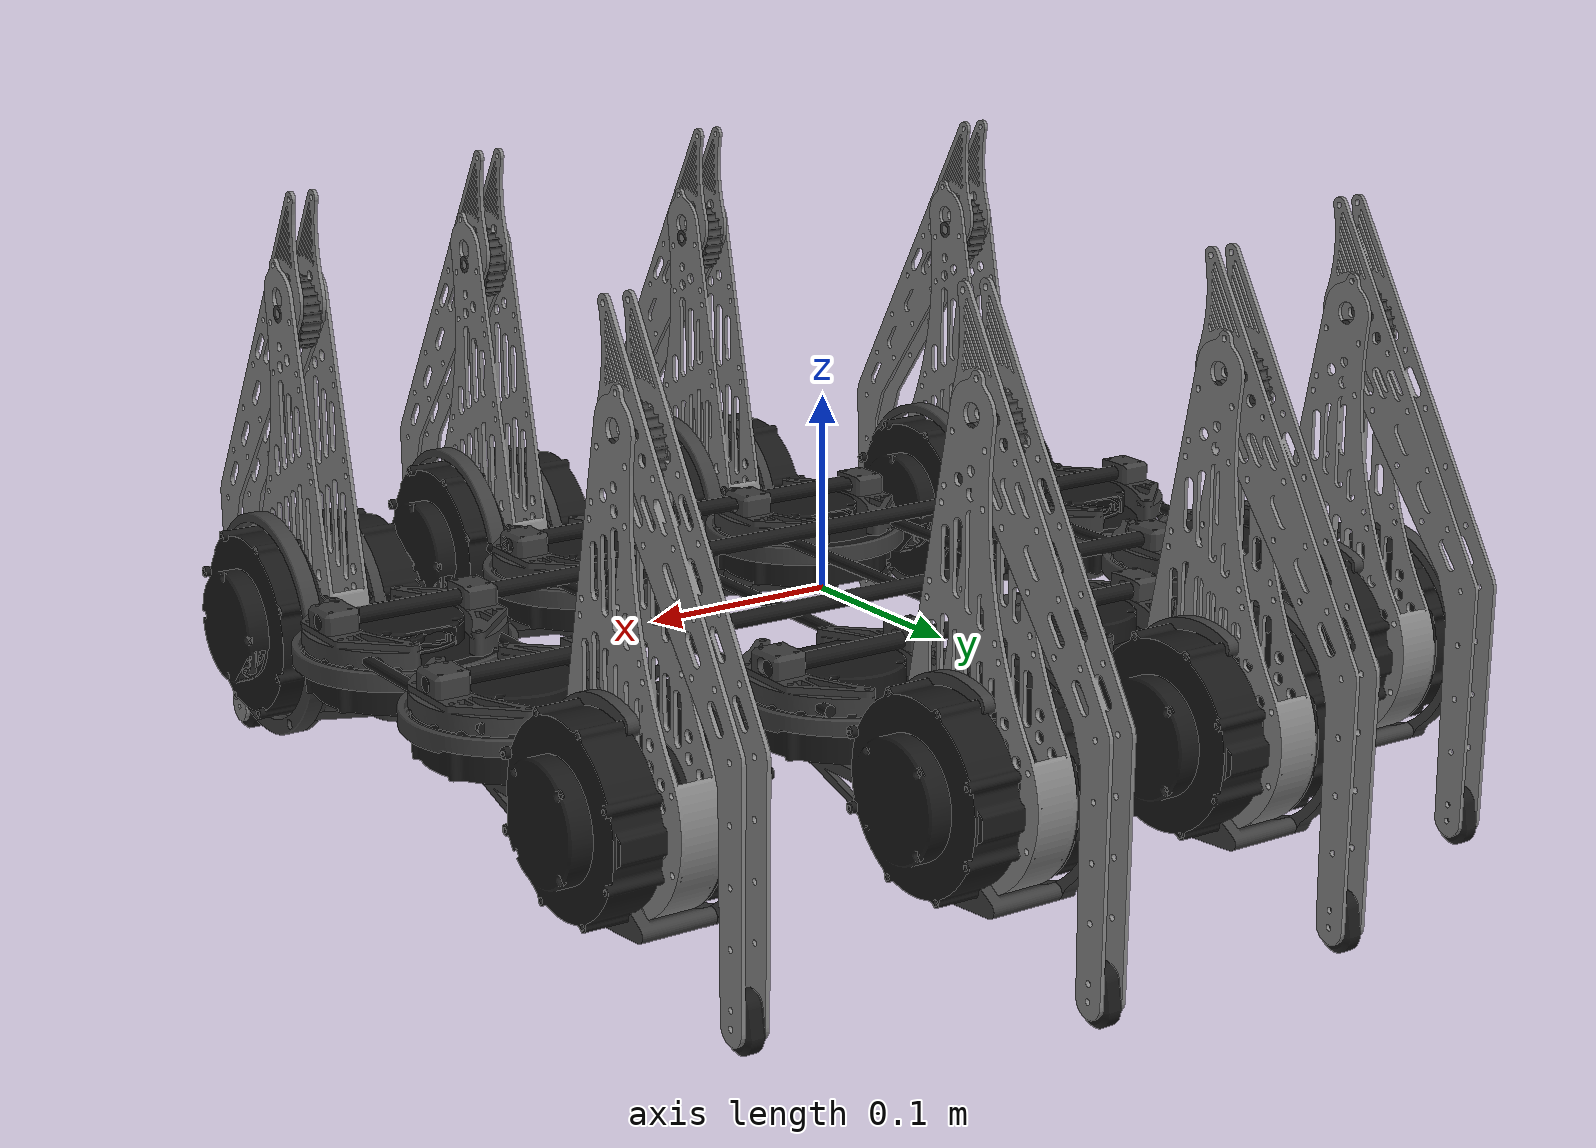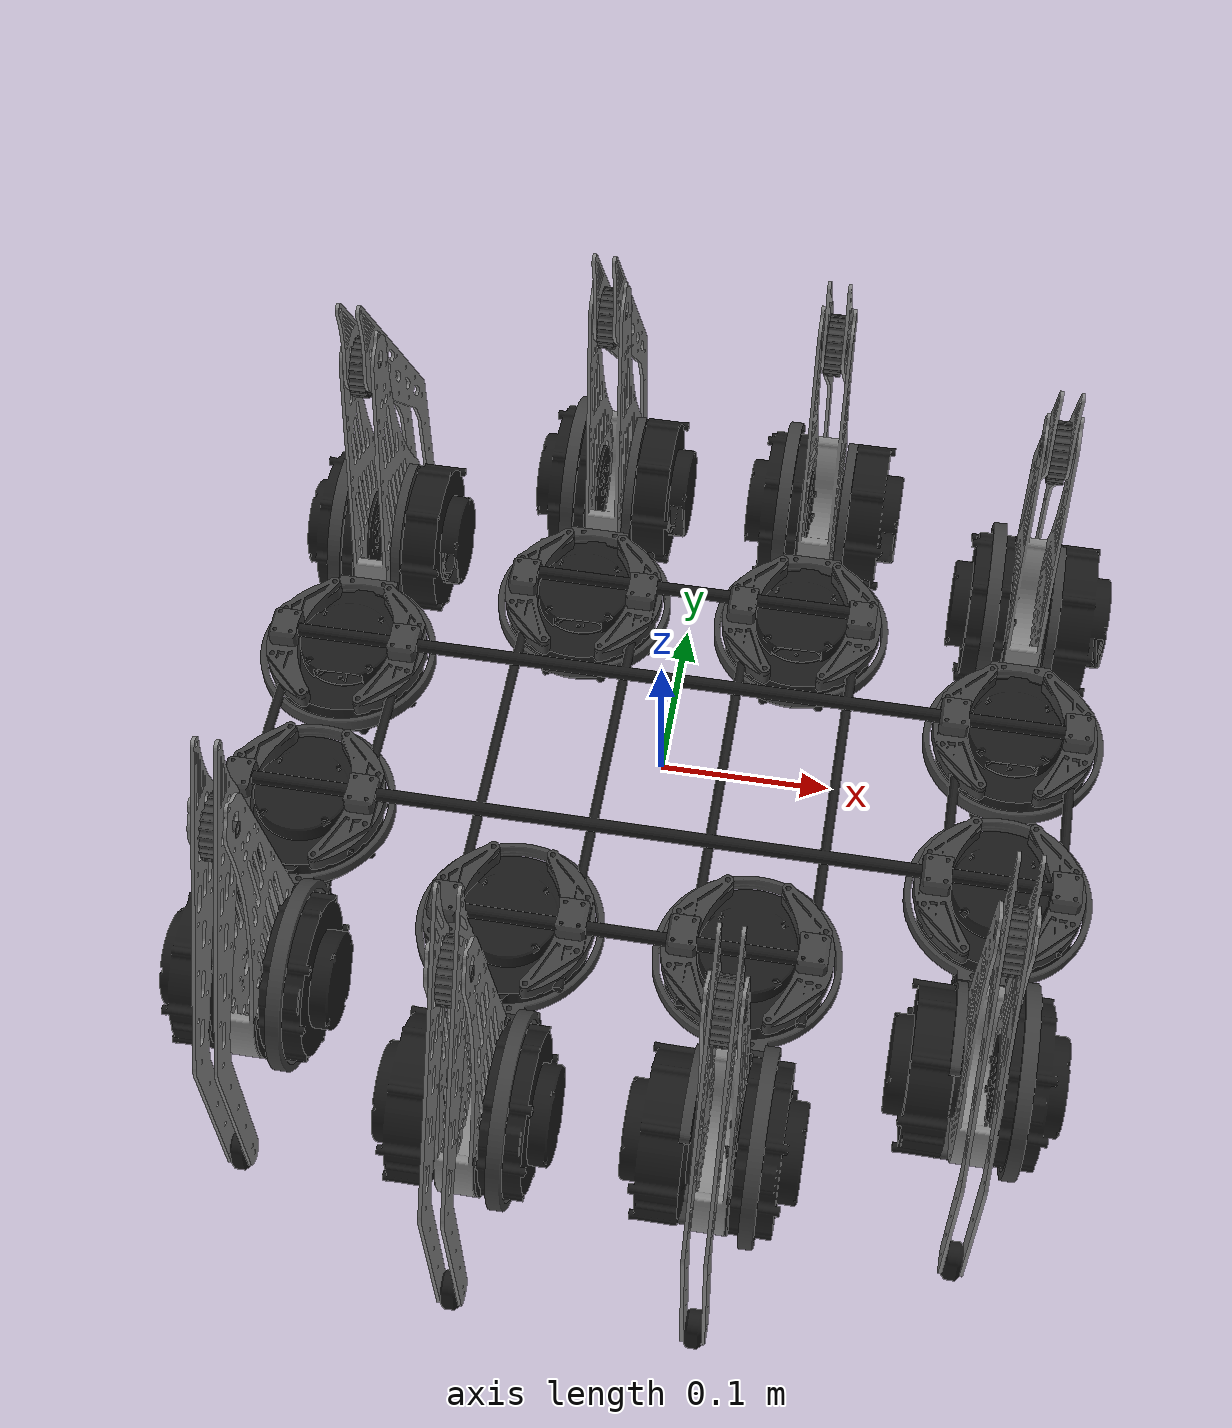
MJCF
<mujoco model="SpiderBot">
    <compiler angle="radian" />
    <default>
        <mesh scale="0.001 0.001 0.001" />
        <geom contype="0" conaffinity="0" group="2" />
        <default class="collision">
            <geom contype="1" conaffinity="1" group="3" pos="0 0 0" mass="0.0" />
        </default>
    </default>
    <asset>
        <mesh name="Body_visual" file="meshes/Body/visual.stl" />
        <mesh name="Body_collision00" file="meshes/Body/collision00.stl" />
        <mesh name="Femur_visual" file="meshes/Femur/visual.stl" />
        <mesh name="Femur_collision00" file="meshes/Femur/collision00.stl" />
        <mesh name="Motor_visual" file="meshes/Motor/visual.stl" />
        <mesh name="Motor_collision00" file="meshes/Motor/collision00.stl" />
        <mesh name="Motor_collision01" file="meshes/Motor/collision01.stl" />
        <mesh name="Motor_collision02" file="meshes/Motor/collision02.stl" />
        <mesh name="Motor_collision03" file="meshes/Motor/collision03.stl" />
        <mesh name="Tibia_visual" file="meshes/Tibia/visual.stl" />
        <mesh name="Tibia_collision00" file="meshes/Tibia/collision00.stl" />
        <mesh name="Tibia_collision01" file="meshes/Tibia/collision01.stl" />
        <mesh name="Tibia_collision02" file="meshes/Tibia/collision02.stl" />
        <mesh name="Tibia_collision03" file="meshes/Tibia/collision03.stl" />
        <mesh name="Knee_visual" file="meshes/Knee/visual.stl" />
        <mesh name="Knee_collision00" file="meshes/Knee/collision00.stl" />
        <mesh name="Knee_collision01" file="meshes/Knee/collision01.stl" />
        <mesh name="Knee_collision02" file="meshes/Knee/collision02.stl" />
        <mesh name="Knee_collision03" file="meshes/Knee/collision03.stl" />
        <mesh name="Knee_collision04" file="meshes/Knee/collision04.stl" />
        <mesh name="Knee_collision05" file="meshes/Knee/collision05.stl" />
        <mesh name="Knee_collision06" file="meshes/Knee/collision06.stl" />
        <mesh name="Foot_visual" file="meshes/Foot/visual.stl" />
        <mesh name="Foot_collision00" file="meshes/Foot/collision00.stl" />
        <mesh name="TibiaBearingTrack_visual" file="meshes/TibiaBearingTrack/visual.stl" />
        <mesh name="TibiaBearingTrack_collision00" file="meshes/TibiaBearingTrack/collision00.stl" />
        <mesh name="TibiaBearingTrack_collision01" file="meshes/TibiaBearingTrack/collision01.stl" />
        <mesh name="TibiaBearingTrack_collision02" file="meshes/TibiaBearingTrack/collision02.stl" />
        <mesh name="TibiaBearingTrack_collision03" file="meshes/TibiaBearingTrack/collision03.stl" />
        <mesh name="TibiaBearingTrack_collision04" file="meshes/TibiaBearingTrack/collision04.stl" />
        <mesh name="TibiaBearingTrack_collision05" file="meshes/TibiaBearingTrack/collision05.stl" />
        <mesh name="TibiaBearingTrack_collision06" file="meshes/TibiaBearingTrack/collision06.stl" />
        <mesh name="TibiaMotorSpacer_visual" file="meshes/TibiaMotorSpacer/visual.stl" />
        <mesh name="TibiaMotorSpacer_collision00" file="meshes/TibiaMotorSpacer/collision00.stl" />
        <mesh name="TibiaMotorSpacer_collision01" file="meshes/TibiaMotorSpacer/collision01.stl" />
        <mesh name="TibiaMotorSpacer_collision02" file="meshes/TibiaMotorSpacer/collision02.stl" />
        <mesh name="TibiaMotorSpacer_collision03" file="meshes/TibiaMotorSpacer/collision03.stl" />
        <mesh name="Hip_visual" file="meshes/Hip/visual.stl" />
        <mesh name="Hip_collision00" file="meshes/Hip/collision00.stl" />
        <mesh name="Hip_collision01" file="meshes/Hip/collision01.stl" />
        <mesh name="Hip_collision02" file="meshes/Hip/collision02.stl" />
        <mesh name="Hip_collision03" file="meshes/Hip/collision03.stl" />
        <mesh name="Hip_collision04" file="meshes/Hip/collision04.stl" />
        <mesh name="HipBearingTrack_visual" file="meshes/HipBearingTrack/visual.stl" />
        <mesh name="HipBearingTrack_collision00" file="meshes/HipBearingTrack/collision00.stl" />
        <mesh name="HipBearingTrack_collision01" file="meshes/HipBearingTrack/collision01.stl" />
        <mesh name="HipBearingTrack_collision02" file="meshes/HipBearingTrack/collision02.stl" />
        <mesh name="HipBearingTrack_collision03" file="meshes/HipBearingTrack/collision03.stl" />
        <mesh name="HipBearingTrack_collision04" file="meshes/HipBearingTrack/collision04.stl" />
        <mesh name="HipBearingTrack_collision05" file="meshes/HipBearingTrack/collision05.stl" />
        <mesh name="HipBearingTrack_collision06" file="meshes/HipBearingTrack/collision06.stl" />
        <mesh name="MainClamp_visual" file="meshes/MainClamp/visual.stl" />
        <mesh name="MainClamp_collision00" file="meshes/MainClamp/collision00.stl" />
        <mesh name="MainClamp_collision01" file="meshes/MainClamp/collision01.stl" />
        <mesh name="MainClamp_collision02" file="meshes/MainClamp/collision02.stl" />
        <mesh name="MainClamp_collision03" file="meshes/MainClamp/collision03.stl" />
        <mesh name="CrossClamp_visual" file="meshes/CrossClamp/visual.stl" />
        <mesh name="CrossClamp_collision00" file="meshes/CrossClamp/collision00.stl" />
        <mesh name="CrossClamp_collision01" file="meshes/CrossClamp/collision01.stl" />
        <material name="Body_mat" rgba="0.0980 0.0980 0.0980 1.0000" roughness="0.0775" />
        <material name="Femur_mat" rgba="0.5373 0.5373 0.5373 1.0000" roughness="0.1225" />
        <material name="Motor_mat" rgba="0.0980 0.0980 0.0980 1.0000" roughness="0.0775" />
        <material name="Tibia_mat" rgba="0.5373 0.5373 0.5373 1.0000" roughness="0.1225" />
        <material name="Knee_mat" rgba="0.2471 0.2471 0.2471 1.0000" roughness="0.2600" />
        <material name="Foot_mat" rgba="0.0980 0.0980 0.0980 1.0000" roughness="0.7071" />
        <material name="TibiaBearingTrack_mat" rgba="0.2471 0.2471 0.2471 1.0000" roughness="0.2600" />
        <material name="TibiaMotorSpacer_mat" rgba="0.0980 0.0980 0.0980 1.0000" roughness="0.7071" />
        <material name="Hip_mat" rgba="0.2471 0.2471 0.2471 1.0000" roughness="0.2600" />
        <material name="HipBearingTrack_mat" rgba="0.2471 0.2471 0.2471 1.0000" roughness="0.2600" />
        <material name="MainClamp_mat" rgba="0.2471 0.2471 0.2471 1.0000" roughness="0.2600" />
        <material name="CrossClamp_mat" rgba="0.2471 0.2471 0.2471 1.0000" roughness="0.2600" />
    </asset>
    <worldbody>
        <body name="Body" pos="0.0 0.0 0.0" quat="1.0 0.0 0.0 0.0">
            <geom mesh="Body_visual" name="Body_Body_visual_geom" type="mesh" pos="0 0 0" quat="1 0 0 0" material="Body_mat" />
            <geom mesh="Body_collision00" name="Body_Body_collision00_geom" type="mesh" pos="0 0 0" quat="1 0 0 0" class="collision" />
            <inertial mass="0.1834360405013815" pos="-0.00022697534267006295 7.111536262824722e-17 0.00728884248412356" fullinertia="0.0011543769717385 0.0032696641298281606 0.004408383882293356 -1.980305755781822e-19 2.2529602229988456e-07 1.533705375905157e-19" />
            <body name="R1_MainClamp" pos="0.21768105157175574 -0.1653739541111095 -0.06824959828188881" quat="0.9999979914074321 -0.002004290672836025 -1.0166845459493043e-15 -2.0377354456429908e-18">
                <geom mesh="MainClamp_visual" name="R1_MainClamp_MainClamp_visual_geom" type="mesh" pos="0 0 0" quat="1 0 0 0" material="MainClamp_mat" />
                <geom mesh="MainClamp_collision00" name="R1_MainClamp_MainClamp_collision00_geom" type="mesh" pos="0 0 0" quat="1 0 0 0" class="collision" />
                <geom mesh="MainClamp_collision01" name="R1_MainClamp_MainClamp_collision01_geom" type="mesh" pos="0 0 0" quat="1 0 0 0" class="collision" />
                <geom mesh="MainClamp_collision02" name="R1_MainClamp_MainClamp_collision02_geom" type="mesh" pos="0 0 0" quat="1 0 0 0" class="collision" />
                <geom mesh="MainClamp_collision03" name="R1_MainClamp_MainClamp_collision03_geom" type="mesh" pos="0 0 0" quat="1 0 0 0" class="collision" />
                <inertial mass="0.04277320346680061" pos="-0.011078641677823025 0.10936584632552593 0.07185120146554273" fullinertia="2.5569324435957536e-05 4.9554608103231195e-05 7.410198303042146e-05 -6.176818167948384e-08 -4.803365145466023e-10 -1.085217966337861e-07" />
                <body name="R1_CrossClamp" pos="0.0 0.0 0.0" quat="1.0 2.168404344971009e-19 9.860682090334649e-32 1.0089855797698544e-35">
                    <geom mesh="CrossClamp_visual" name="R1_CrossClamp_CrossClamp_visual_geom" type="mesh" pos="0 0 0" quat="1 0 0 0" material="CrossClamp_mat" />
                    <geom mesh="CrossClamp_collision00" name="R1_CrossClamp_CrossClamp_collision00_geom" type="mesh" pos="0 0 0" quat="1 0 0 0" class="collision" />
                    <geom mesh="CrossClamp_collision01" name="R1_CrossClamp_CrossClamp_collision01_geom" type="mesh" pos="0 0 0" quat="1 0 0 0" class="collision" />
                    <inertial mass="0.0060873366326105825" pos="-0.011076095384506187 0.10937852181993969 0.08220436514827456" fullinertia="3.569640975298384e-07 8.628331172516547e-06 8.861345261438887e-06 -2.3998371452414035e-08 -9.439137922445104e-11 -1.065146252732629e-09" />
                </body>
                <body name="R1_Hip-assembly_Motor" pos="-0.011076386363475165 0.10966822722227196 0.01505997107270793" quat="-0.0014172475262309893 0.707105360897122 0.001417247526231073 -0.7071053608971223">
                    <geom mesh="Motor_visual" name="R1_Hip-assembly_Motor_Motor_visual_geom" type="mesh" pos="0 0 0" quat="1 0 0 0" material="Motor_mat" />
                    <geom mesh="Motor_collision00" name="R1_Hip-assembly_Motor_Motor_collision00_geom" type="mesh" pos="0 0 0" quat="1 0 0 0" class="collision" />
                    <geom mesh="Motor_collision01" name="R1_Hip-assembly_Motor_Motor_collision01_geom" type="mesh" pos="0 0 0" quat="1 0 0 0" class="collision" />
                    <geom mesh="Motor_collision02" name="R1_Hip-assembly_Motor_Motor_collision02_geom" type="mesh" pos="0 0 0" quat="1 0 0 0" class="collision" />
                    <geom mesh="Motor_collision03" name="R1_Hip-assembly_Motor_Motor_collision03_geom" type="mesh" pos="0 0 0" quat="1 0 0 0" class="collision" />
                    <inertial mass="0.4096463210987154" pos="-0.03569820729651781 0.00047016950890323497 -5.891982746499138e-06" fullinertia="0.0004025220023127328 0.00022651206716561785 0.00023297814211205612 1.5369569971653381e-06 -5.181750872317603e-08 -2.6262635187278443e-08" />
                    <body name="R1_Hip" pos="0.014620638666750292 0.10750000000000089 -0.010029361333295093" quat="1.2699325361584729e-15 -0.7071067811865472 1.102379038134243e-15 0.7071067811865478">
                        <joint type="hinge" name="R1_Hip" axis="2.04862431470163e-15 2.5916768731093498e-15 1.0" pos="-0.01002902654157561 0.10750023900524656 0.035250000000043864" range="-1.396263 1.396263" limited="true" />
                        <geom mesh="Hip_visual" name="R1_Hip_Hip_visual_geom" type="mesh" pos="0 0 0" quat="1 0 0 0" material="Hip_mat" />
                        <geom mesh="Hip_collision00" name="R1_Hip_Hip_collision00_geom" type="mesh" pos="0 0 0" quat="1 0 0 0" class="collision" />
                        <geom mesh="Hip_collision01" name="R1_Hip_Hip_collision01_geom" type="mesh" pos="0 0 0" quat="1 0 0 0" class="collision" />
                        <geom mesh="Hip_collision02" name="R1_Hip_Hip_collision02_geom" type="mesh" pos="0 0 0" quat="1 0 0 0" class="collision" />
                        <geom mesh="Hip_collision03" name="R1_Hip_Hip_collision03_geom" type="mesh" pos="0 0 0" quat="1 0 0 0" class="collision" />
                        <geom mesh="Hip_collision04" name="R1_Hip_Hip_collision04_geom" type="mesh" pos="0 0 0" quat="1 0 0 0" class="collision" />
                        <inertial mass="0.052580342819792604" pos="-0.012181480181525596 0.04674400290943466 0.02883739744027624" fullinertia="0.00011036308582381741 3.7076315879304005e-05 8.929956210807947e-05 -2.9193347098827487e-06 4.020625400927333e-06 -1.4395949292889949e-05" />
                        <body name="R1_HipBearingTrack" pos="0.0010470250301800378 -0.0022277151058630196 4.017181553184202e-07" quat="0.9999979914074321 -0.0020042906728373207 7.502826567872053e-18 6.124750082395104e-17">
                            <geom mesh="HipBearingTrack_visual" name="R1_HipBearingTrack_HipBearingTrack_visual_geom" type="mesh" pos="0 0 0" quat="1 0 0 0" material="HipBearingTrack_mat" />
                            <geom mesh="HipBearingTrack_collision00" name="R1_HipBearingTrack_HipBearingTrack_collision00_geom" type="mesh" pos="0 0 0" quat="1 0 0 0" class="collision" />
                            <geom mesh="HipBearingTrack_collision01" name="R1_HipBearingTrack_HipBearingTrack_collision01_geom" type="mesh" pos="0 0 0" quat="1 0 0 0" class="collision" />
                            <geom mesh="HipBearingTrack_collision02" name="R1_HipBearingTrack_HipBearingTrack_collision02_geom" type="mesh" pos="0 0 0" quat="1 0 0 0" class="collision" />
                            <geom mesh="HipBearingTrack_collision03" name="R1_HipBearingTrack_HipBearingTrack_collision03_geom" type="mesh" pos="0 0 0" quat="1 0 0 0" class="collision" />
                            <geom mesh="HipBearingTrack_collision04" name="R1_HipBearingTrack_HipBearingTrack_collision04_geom" type="mesh" pos="0 0 0" quat="1 0 0 0" class="collision" />
                            <geom mesh="HipBearingTrack_collision05" name="R1_HipBearingTrack_HipBearingTrack_collision05_geom" type="mesh" pos="0 0 0" quat="1 0 0 0" class="collision" />
                            <geom mesh="HipBearingTrack_collision06" name="R1_HipBearingTrack_HipBearingTrack_collision06_geom" type="mesh" pos="0 0 0" quat="1 0 0 0" class="collision" />
                            <inertial mass="0.011609757728843081" pos="-0.010935890023697522 0.10786068092028847 0.06071584524702324" fullinertia="1.748494583348385e-05 1.5363892724198782e-05 3.26918707448008e-05 8.956505581896182e-08 2.8681776478974446e-09 1.1403857006667951e-07" />
                        </body>
                        <body name="R1_Femur-assembly_Motor" pos="3.552713678800501e-17 -3.1974423109204507e-16 0.0500000000000013" quat="-6.114900252818196e-17 1.0 6.126241564798603e-17 -2.2907194013402957e-29">
                            <geom mesh="Motor_visual" name="R1_Femur-assembly_Motor_Motor_visual_geom" type="mesh" pos="0 0 0" quat="1 0 0 0" material="Motor_mat" />
                            <geom mesh="Motor_collision00" name="R1_Femur-assembly_Motor_Motor_collision00_geom" type="mesh" pos="0 0 0" quat="1 0 0 0" class="collision" />
                            <geom mesh="Motor_collision01" name="R1_Femur-assembly_Motor_Motor_collision01_geom" type="mesh" pos="0 0 0" quat="1 0 0 0" class="collision" />
                            <geom mesh="Motor_collision02" name="R1_Femur-assembly_Motor_Motor_collision02_geom" type="mesh" pos="0 0 0" quat="1 0 0 0" class="collision" />
                            <geom mesh="Motor_collision03" name="R1_Femur-assembly_Motor_Motor_collision03_geom" type="mesh" pos="0 0 0" quat="1 0 0 0" class="collision" />
                            <inertial mass="0.4096463210987154" pos="-0.03569820729651777 0.0004701695089032045 -5.891982746489858e-06" fullinertia="0.00040252200231273225 0.00022651206716561866 0.0002329781421120602 1.5369569971637052e-06 -5.181750872274396e-08 -2.626263518655713e-08" />
                            <body name="R1_Femur" pos="0.0 -2.1316282072803005e-16 0.04999999999999993" quat="-2.609024107869118e-15 0.9999999999999999 -3.5582322627219784e-34 3.022776199361025e-32">
                                <joint type="hinge" name="R1_Femur" axis="-1.0 6.015138125580519e-20 2.048624314701585e-15" pos="-0.02062902654157562 2.390052469627731e-07 0.050000000000042816" range="-1.570796 0.0" limited="true" />
                                <geom mesh="Femur_visual" name="R1_Femur_Femur_visual_geom" type="mesh" pos="0 0 0" quat="1 0 0 0" material="Femur_mat" />
                                <geom mesh="Femur_collision00" name="R1_Femur_Femur_collision00_geom" type="mesh" pos="0 0 0" quat="1 0 0 0" class="collision" />
                                <inertial mass="0.230842936042845" pos="-0.01038368677116484 0.0008485718996991484 0.051461139330156426" fullinertia="0.0008028766514152899 0.0005773602804628149 0.0002491128346876032 -6.940768618269669e-08 2.303269615935221e-08 -1.470243222718049e-05" />
                                <body name="R1_TibiaMotorSpacer" pos="0.0 0.0 0.0" quat="1.0 0.0 0.0 -7.821578647613801e-46">
                                    <geom mesh="TibiaMotorSpacer_visual" name="R1_TibiaMotorSpacer_TibiaMotorSpacer_visual_geom" type="mesh" pos="0 0 0" quat="1 0 0 0" material="TibiaMotorSpacer_mat" />
                                    <geom mesh="TibiaMotorSpacer_collision00" name="R1_TibiaMotorSpacer_TibiaMotorSpacer_collision00_geom" type="mesh" pos="0 0 0" quat="1 0 0 0" class="collision" />
                                    <geom mesh="TibiaMotorSpacer_collision01" name="R1_TibiaMotorSpacer_TibiaMotorSpacer_collision01_geom" type="mesh" pos="0 0 0" quat="1 0 0 0" class="collision" />
                                    <geom mesh="TibiaMotorSpacer_collision02" name="R1_TibiaMotorSpacer_TibiaMotorSpacer_collision02_geom" type="mesh" pos="0 0 0" quat="1 0 0 0" class="collision" />
                                    <geom mesh="TibiaMotorSpacer_collision03" name="R1_TibiaMotorSpacer_TibiaMotorSpacer_collision03_geom" type="mesh" pos="0 0 0" quat="1 0 0 0" class="collision" />
                                    <inertial mass="0.01707263849756077" pos="0.0013206386667055162 -6.945183746737574e-06 0.029478113737471095" fullinertia="2.92110253484819e-05 7.473002877028613e-06 2.1744424710889478e-05 6.376845803731863e-24 3.8913849235565664e-20 3.751013704944496e-09" />
                                    <body name="R1_Tibia-assembly_Motor" pos="-0.02405872266658843 4.618527782440651e-16 0.05000000206997373" quat="-2.312169521622237e-16 7.20464942823445e-16 0.38268343236509045 0.9238795325112871">
                                        <geom mesh="Motor_visual" name="R1_Tibia-assembly_Motor_Motor_visual_geom" type="mesh" pos="0 0 0" quat="1 0 0 0" material="Motor_mat" />
                                        <geom mesh="Motor_collision00" name="R1_Tibia-assembly_Motor_Motor_collision00_geom" type="mesh" pos="0 0 0" quat="1 0 0 0" class="collision" />
                                        <geom mesh="Motor_collision01" name="R1_Tibia-assembly_Motor_Motor_collision01_geom" type="mesh" pos="0 0 0" quat="1 0 0 0" class="collision" />
                                        <geom mesh="Motor_collision02" name="R1_Tibia-assembly_Motor_Motor_collision02_geom" type="mesh" pos="0 0 0" quat="1 0 0 0" class="collision" />
                                        <geom mesh="Motor_collision03" name="R1_Tibia-assembly_Motor_Motor_collision03_geom" type="mesh" pos="0 0 0" quat="1 0 0 0" class="collision" />
                                        <inertial mass="0.4096463210987154" pos="-0.03569820729651784 0.0004701695089032192 -5.89198274647266e-06" fullinertia="0.00040252200231273474 0.0002265120671656241 0.00023297814211206257 1.5369569971684014e-06 -5.181750872574426e-08 -2.6262635184664784e-08" />
                                    </body>
                                </body>
                                <body name="R1_Knee" pos="-0.015029361333294489 -0.019714907448651217 0.17395842405625625" quat="1.0 0.0 8.048094238931602e-20 -2.0619978725023343e-37">
                                    <joint type="hinge" name="R1_Knee" axis="-1.0 6.015138125580519e-20 2.0484633528168065e-15" pos="0.014000334791719178 0.01971514645389945 0.03304157594378652" range="-0.20944 2.268928" limited="true" />
                                    <geom mesh="Knee_visual" name="R1_Knee_Knee_visual_geom" type="mesh" pos="0 0 0" quat="1 0 0 0" material="Knee_mat" />
                                    <geom mesh="Knee_collision00" name="R1_Knee_Knee_collision00_geom" type="mesh" pos="0 0 0" quat="1 0 0 0" class="collision" />
                                    <geom mesh="Knee_collision01" name="R1_Knee_Knee_collision01_geom" type="mesh" pos="0 0 0" quat="1 0 0 0" class="collision" />
                                    <geom mesh="Knee_collision02" name="R1_Knee_Knee_collision02_geom" type="mesh" pos="0 0 0" quat="1 0 0 0" class="collision" />
                                    <geom mesh="Knee_collision03" name="R1_Knee_Knee_collision03_geom" type="mesh" pos="0 0 0" quat="1 0 0 0" class="collision" />
                                    <geom mesh="Knee_collision04" name="R1_Knee_Knee_collision04_geom" type="mesh" pos="0 0 0" quat="1 0 0 0" class="collision" />
                                    <geom mesh="Knee_collision05" name="R1_Knee_Knee_collision05_geom" type="mesh" pos="0 0 0" quat="1 0 0 0" class="collision" />
                                    <geom mesh="Knee_collision06" name="R1_Knee_Knee_collision06_geom" type="mesh" pos="0 0 0" quat="1 0 0 0" class="collision" />
                                    <inertial mass="0.008812389430275673" pos="0.004999999999999997 0.01971490744850877 0.03304157594374378" fullinertia="1.4471797213983146e-06 8.008801325288346e-07 8.008801268247386e-07 -3.887588583671627e-26 5.2886187589850886e-20 -3.577867169206689e-17" />
                                    <body name="R1_Tibia" pos="0.015029361333294489 0.019714907448651255 -0.17395842405625622" quat="1.0 0.0 -8.048094238931602e-20 1.6959068022287468e-22">
                                        <geom mesh="Tibia_visual" name="R1_Tibia_Tibia_visual_geom" type="mesh" pos="0 0 0" quat="1 0 0 0" material="Tibia_mat" />
                                        <geom mesh="Tibia_collision00" name="R1_Tibia_Tibia_collision00_geom" type="mesh" pos="0 0 0" quat="1 0 0 0" class="collision" />
                                        <geom mesh="Tibia_collision01" name="R1_Tibia_Tibia_collision01_geom" type="mesh" pos="0 0 0" quat="1 0 0 0" class="collision" />
                                        <geom mesh="Tibia_collision02" name="R1_Tibia_Tibia_collision02_geom" type="mesh" pos="0 0 0" quat="1 0 0 0" class="collision" />
                                        <geom mesh="Tibia_collision03" name="R1_Tibia_Tibia_collision03_geom" type="mesh" pos="0 0 0" quat="1 0 0 0" class="collision" />
                                        <inertial mass="0.07297107048801112" pos="-0.010029361333294318 -0.047571361468123095 0.11810916584738512" fullinertia="0.0005482843792552127 0.0004624716132690046 9.11153304416727e-05 9.28048459449213e-19 7.981448332518919e-19 -0.00018206801217491339" />
                                        <body name="R1_Foot" pos="0.0 0.0 0.0" quat="1.0 0.0 0.0 -7.821578647613801e-46">
                                            <geom mesh="Foot_visual" name="R1_Foot_Foot_visual_geom" type="mesh" pos="0 0 0" quat="1 0 0 0" material="Foot_mat" />
                                            <geom mesh="Foot_collision00" name="R1_Foot_Foot_collision00_geom" type="mesh" pos="0 0 0" quat="1 0 0 0" class="collision" />
                                            <inertial mass="0.004818206956885" pos="-0.010029361333294169 -0.08392600723875258 -0.03482830039342609" fullinertia="4.0355141511761675e-07 3.266830345812974e-07 1.499315714350788e-07 5.421149125806025e-20 -5.195717374964061e-22 6.771781368874443e-10" />
                                        </body>
                                    </body>
                                </body>
                            </body>
                        </body>
                        <body name="R1_TibiaBearingTrack" pos="3.552713678800501e-17 -1.0658141036401502e-16 1.3500311979441904e-15" quat="1.0 2.6701731103973003e-15 2.297557386456197e-29 6.126241564798602e-17">
                            <geom mesh="TibiaBearingTrack_visual" name="R1_TibiaBearingTrack_TibiaBearingTrack_visual_geom" type="mesh" pos="0 0 0" quat="1 0 0 0" material="TibiaBearingTrack_mat" />
                            <geom mesh="TibiaBearingTrack_collision00" name="R1_TibiaBearingTrack_TibiaBearingTrack_collision00_geom" type="mesh" pos="0 0 0" quat="1 0 0 0" class="collision" />
                            <geom mesh="TibiaBearingTrack_collision01" name="R1_TibiaBearingTrack_TibiaBearingTrack_collision01_geom" type="mesh" pos="0 0 0" quat="1 0 0 0" class="collision" />
                            <geom mesh="TibiaBearingTrack_collision02" name="R1_TibiaBearingTrack_TibiaBearingTrack_collision02_geom" type="mesh" pos="0 0 0" quat="1 0 0 0" class="collision" />
                            <geom mesh="TibiaBearingTrack_collision03" name="R1_TibiaBearingTrack_TibiaBearingTrack_collision03_geom" type="mesh" pos="0 0 0" quat="1 0 0 0" class="collision" />
                            <geom mesh="TibiaBearingTrack_collision04" name="R1_TibiaBearingTrack_TibiaBearingTrack_collision04_geom" type="mesh" pos="0 0 0" quat="1 0 0 0" class="collision" />
                            <geom mesh="TibiaBearingTrack_collision05" name="R1_TibiaBearingTrack_TibiaBearingTrack_collision05_geom" type="mesh" pos="0 0 0" quat="1 0 0 0" class="collision" />
                            <geom mesh="TibiaBearingTrack_collision06" name="R1_TibiaBearingTrack_TibiaBearingTrack_collision06_geom" type="mesh" pos="0 0 0" quat="1 0 0 0" class="collision" />
                            <inertial mass="0.015140027390716102" pos="0.012936002208848415 0.008673353142335503 0.03817888888858537" fullinertia="4.130276155873871e-05 2.106701364111607e-05 2.040326746851044e-05 2.923768935302156e-10 -2.5812677988877467e-09 4.89867294516e-07" />
                        </body>
                    </body>
                </body>
            </body>
            <body name="L1_MainClamp" pos="0.19552827884480486 0.16537395411110978 -0.06824959828188862" quat="3.304566878248689e-18 1.648743011932669e-15 -0.0020042906728360193 0.9999979914074331">
                <geom mesh="MainClamp_visual" name="L1_MainClamp_MainClamp_visual_geom" type="mesh" pos="0 0 0" quat="1 0 0 0" material="MainClamp_mat" />
                <geom mesh="MainClamp_collision00" name="L1_MainClamp_MainClamp_collision00_geom" type="mesh" pos="0 0 0" quat="1 0 0 0" class="collision" />
                <geom mesh="MainClamp_collision01" name="L1_MainClamp_MainClamp_collision01_geom" type="mesh" pos="0 0 0" quat="1 0 0 0" class="collision" />
                <geom mesh="MainClamp_collision02" name="L1_MainClamp_MainClamp_collision02_geom" type="mesh" pos="0 0 0" quat="1 0 0 0" class="collision" />
                <geom mesh="MainClamp_collision03" name="L1_MainClamp_MainClamp_collision03_geom" type="mesh" pos="0 0 0" quat="1 0 0 0" class="collision" />
                <inertial mass="0.04277320346680061" pos="-0.011078641677823117 0.1093658463255267 0.07185120146554273" fullinertia="2.5569324435959454e-05 4.95546081032322e-05 7.410198303041624e-05 -6.176818167937585e-08 -4.803365145559676e-10 -1.0852179663381e-07" />
                <body name="L1_CrossClamp" pos="0.0 0.0 0.0" quat="1.0 2.1689618408400908e-19 9.865514810942556e-32 -1.6059710305357113e-33">
                    <geom mesh="CrossClamp_visual" name="L1_CrossClamp_CrossClamp_visual_geom" type="mesh" pos="0 0 0" quat="1 0 0 0" material="CrossClamp_mat" />
                    <geom mesh="CrossClamp_collision00" name="L1_CrossClamp_CrossClamp_collision00_geom" type="mesh" pos="0 0 0" quat="1 0 0 0" class="collision" />
                    <geom mesh="CrossClamp_collision01" name="L1_CrossClamp_CrossClamp_collision01_geom" type="mesh" pos="0 0 0" quat="1 0 0 0" class="collision" />
                    <inertial mass="0.0060873366326105825" pos="-0.01107609538450623 0.10937852181994043 0.08220436514827456" fullinertia="3.569640975301696e-07 8.628331172516879e-06 8.861345261438236e-06 -2.3998371452427766e-08 -9.439137922391922e-11 -1.0651462527322915e-09" />
                </body>
                <body name="L1_Hip-assembly_Motor" pos="-0.011076386363475165 0.10966822722227194 0.015059971072707939" quat="-0.0014172475262309893 0.707105360897122 0.001417247526231073 -0.7071053608971223">
                    <geom mesh="Motor_visual" name="L1_Hip-assembly_Motor_Motor_visual_geom" type="mesh" pos="0 0 0" quat="1 0 0 0" material="Motor_mat" />
                    <geom mesh="Motor_collision00" name="L1_Hip-assembly_Motor_Motor_collision00_geom" type="mesh" pos="0 0 0" quat="1 0 0 0" class="collision" />
                    <geom mesh="Motor_collision01" name="L1_Hip-assembly_Motor_Motor_collision01_geom" type="mesh" pos="0 0 0" quat="1 0 0 0" class="collision" />
                    <geom mesh="Motor_collision02" name="L1_Hip-assembly_Motor_Motor_collision02_geom" type="mesh" pos="0 0 0" quat="1 0 0 0" class="collision" />
                    <geom mesh="Motor_collision03" name="L1_Hip-assembly_Motor_Motor_collision03_geom" type="mesh" pos="0 0 0" quat="1 0 0 0" class="collision" />
                    <inertial mass="0.4096463210987154" pos="-0.03569820729651781 0.0004701695089032278 -5.891982746508759e-06" fullinertia="0.0004025220023127328 0.00022651206716561948 0.0002329781421120636 1.5369569971652288e-06 -5.181750872296188e-08 -2.6262635188144045e-08" />
                    <body name="L1_Hip" pos="0.014620638666750292 0.10750000000000093 -0.010029361333295128" quat="1.2699325361584729e-15 -0.7071067811865472 1.1023790381342386e-15 0.7071067811865478">
                        <joint type="hinge" name="L1_Hip" axis="3.312743785769343e-15 2.5916768731093498e-15 1.0" pos="-0.010029696125015048 0.10750023900524724 0.03525000000004368" range="-1.396263 1.396263" limited="true" />
                        <geom mesh="Hip_visual" name="L1_Hip_Hip_visual_geom" type="mesh" pos="0 0 0" quat="1 0 0 0" material="Hip_mat" />
                        <geom mesh="Hip_collision00" name="L1_Hip_Hip_collision00_geom" type="mesh" pos="0 0 0" quat="1 0 0 0" class="collision" />
                        <geom mesh="Hip_collision01" name="L1_Hip_Hip_collision01_geom" type="mesh" pos="0 0 0" quat="1 0 0 0" class="collision" />
                        <geom mesh="Hip_collision02" name="L1_Hip_Hip_collision02_geom" type="mesh" pos="0 0 0" quat="1 0 0 0" class="collision" />
                        <geom mesh="Hip_collision03" name="L1_Hip_Hip_collision03_geom" type="mesh" pos="0 0 0" quat="1 0 0 0" class="collision" />
                        <geom mesh="Hip_collision04" name="L1_Hip_Hip_collision04_geom" type="mesh" pos="0 0 0" quat="1 0 0 0" class="collision" />
                        <inertial mass="0.052580342819792604" pos="-0.012181480181525711 0.046744002909435 0.028837397440276236" fullinertia="0.0001103630858238195 3.707631587930513e-05 8.92995621080786e-05 -2.9193347098832213e-06 4.020625400927158e-06 -1.4395949292890052e-05" />
                        <body name="L1_HipBearingTrack" pos="0.0010470250301800378 -0.002227715105862984 4.017181553184202e-07" quat="0.9999979914074321 -0.0020042906728373207 7.502826567872045e-18 6.124750082395104e-17">
                            <geom mesh="HipBearingTrack_visual" name="L1_HipBearingTrack_HipBearingTrack_visual_geom" type="mesh" pos="0 0 0" quat="1 0 0 0" material="HipBearingTrack_mat" />
                            <geom mesh="HipBearingTrack_collision00" name="L1_HipBearingTrack_HipBearingTrack_collision00_geom" type="mesh" pos="0 0 0" quat="1 0 0 0" class="collision" />
                            <geom mesh="HipBearingTrack_collision01" name="L1_HipBearingTrack_HipBearingTrack_collision01_geom" type="mesh" pos="0 0 0" quat="1 0 0 0" class="collision" />
                            <geom mesh="HipBearingTrack_collision02" name="L1_HipBearingTrack_HipBearingTrack_collision02_geom" type="mesh" pos="0 0 0" quat="1 0 0 0" class="collision" />
                            <geom mesh="HipBearingTrack_collision03" name="L1_HipBearingTrack_HipBearingTrack_collision03_geom" type="mesh" pos="0 0 0" quat="1 0 0 0" class="collision" />
                            <geom mesh="HipBearingTrack_collision04" name="L1_HipBearingTrack_HipBearingTrack_collision04_geom" type="mesh" pos="0 0 0" quat="1 0 0 0" class="collision" />
                            <geom mesh="HipBearingTrack_collision05" name="L1_HipBearingTrack_HipBearingTrack_collision05_geom" type="mesh" pos="0 0 0" quat="1 0 0 0" class="collision" />
                            <geom mesh="HipBearingTrack_collision06" name="L1_HipBearingTrack_HipBearingTrack_collision06_geom" type="mesh" pos="0 0 0" quat="1 0 0 0" class="collision" />
                            <inertial mass="0.011609757728843081" pos="-0.010935890023697591 0.1078606809202892 0.06071584524702323" fullinertia="1.7484945833484434e-05 1.5363892724199433e-05 3.2691870744799935e-05 8.956505581898975e-08 2.868177647906621e-09 1.140385700666493e-07" />
                        </body>
                        <body name="L1_Femur-assembly_Motor" pos="0.0 -2.486899575160351e-16 0.0500000000000013" quat="-6.114900252818186e-17 1.0 6.126241564798603e-17 -2.2948931854515965e-29">
                            <geom mesh="Motor_visual" name="L1_Femur-assembly_Motor_Motor_visual_geom" type="mesh" pos="0 0 0" quat="1 0 0 0" material="Motor_mat" />
                            <geom mesh="Motor_collision00" name="L1_Femur-assembly_Motor_Motor_collision00_geom" type="mesh" pos="0 0 0" quat="1 0 0 0" class="collision" />
                            <geom mesh="Motor_collision01" name="L1_Femur-assembly_Motor_Motor_collision01_geom" type="mesh" pos="0 0 0" quat="1 0 0 0" class="collision" />
                            <geom mesh="Motor_collision02" name="L1_Femur-assembly_Motor_Motor_collision02_geom" type="mesh" pos="0 0 0" quat="1 0 0 0" class="collision" />
                            <geom mesh="Motor_collision03" name="L1_Femur-assembly_Motor_Motor_collision03_geom" type="mesh" pos="0 0 0" quat="1 0 0 0" class="collision" />
                            <inertial mass="0.4096463210987154" pos="-0.03569820729651801 0.0004701695089032062 -5.891982746488369e-06" fullinertia="0.00040252200231273507 0.00022651206716562717 0.0002329781421120602 1.536956997165451e-06 -5.1817508723180395e-08 -2.6262635186778406e-08" />
                            <body name="L1_Femur" pos="0.0 -1.7763568394002506e-16 0.04999999999999992" quat="-2.6090241078691135e-15 0.9999999999999999 1.0675054281976233e-34 -2.238572363512608e-31">
                                <joint type="hinge" name="L1_Femur" axis="-1.0000000000000036 6.015138126582773e-20 3.312743785769286e-15" pos="-0.02062969612501502 2.390052472680853e-07 0.05000000000004265" range="-1.570796 0.0" limited="true" />
                                <geom mesh="Femur_visual" name="L1_Femur_Femur_visual_geom" type="mesh" pos="0 0 0" quat="1 0 0 0" material="Femur_mat" />
                                <geom mesh="Femur_collision00" name="L1_Femur_Femur_collision00_geom" type="mesh" pos="0 0 0" quat="1 0 0 0" class="collision" />
                                <inertial mass="0.230842936042845" pos="-0.010383686771164883 0.0008485718996991514 0.05146113933015643" fullinertia="0.0008028766514153051 0.0005773602804628295 0.0002491128346876067 -6.94076861818484e-08 2.3032696159194377e-08 -1.4702432227180668e-05" />
                                <body name="L1_TibiaMotorSpacer" pos="0.0 0.0 0.0" quat="1.0 0.0 0.0 3.490722164698665e-36">
                                    <geom mesh="TibiaMotorSpacer_visual" name="L1_TibiaMotorSpacer_TibiaMotorSpacer_visual_geom" type="mesh" pos="0 0 0" quat="1 0 0 0" material="TibiaMotorSpacer_mat" />
                                    <geom mesh="TibiaMotorSpacer_collision00" name="L1_TibiaMotorSpacer_TibiaMotorSpacer_collision00_geom" type="mesh" pos="0 0 0" quat="1 0 0 0" class="collision" />
                                    <geom mesh="TibiaMotorSpacer_collision01" name="L1_TibiaMotorSpacer_TibiaMotorSpacer_collision01_geom" type="mesh" pos="0 0 0" quat="1 0 0 0" class="collision" />
                                    <geom mesh="TibiaMotorSpacer_collision02" name="L1_TibiaMotorSpacer_TibiaMotorSpacer_collision02_geom" type="mesh" pos="0 0 0" quat="1 0 0 0" class="collision" />
                                    <geom mesh="TibiaMotorSpacer_collision03" name="L1_TibiaMotorSpacer_TibiaMotorSpacer_collision03_geom" type="mesh" pos="0 0 0" quat="1 0 0 0" class="collision" />
                                    <inertial mass="0.01707263849756077" pos="0.0013206386667055229 -6.945183746737599e-06 0.029478113737471095" fullinertia="2.9211025348482436e-05 7.473002877029099e-06 2.1744424710889694e-05 1.0843133582381545e-19 2.947517398689744e-20 3.7510137049578544e-09" />
                                    <body name="L1_Tibia-assembly_Motor" pos="-0.024058722666588466 4.618527782440651e-16 0.05000000206997373" quat="-2.3121695216222366e-16 7.20464942823445e-16 0.38268343236509034 0.9238795325112871">
                                        <geom mesh="Motor_visual" name="L1_Tibia-assembly_Motor_Motor_visual_geom" type="mesh" pos="0 0 0" quat="1 0 0 0" material="Motor_mat" />
                                        <geom mesh="Motor_collision00" name="L1_Tibia-assembly_Motor_Motor_collision00_geom" type="mesh" pos="0 0 0" quat="1 0 0 0" class="collision" />
                                        <geom mesh="Motor_collision01" name="L1_Tibia-assembly_Motor_Motor_collision01_geom" type="mesh" pos="0 0 0" quat="1 0 0 0" class="collision" />
                                        <geom mesh="Motor_collision02" name="L1_Tibia-assembly_Motor_Motor_collision02_geom" type="mesh" pos="0 0 0" quat="1 0 0 0" class="collision" />
                                        <geom mesh="Motor_collision03" name="L1_Tibia-assembly_Motor_Motor_collision03_geom" type="mesh" pos="0 0 0" quat="1 0 0 0" class="collision" />
                                        <inertial mass="0.4096463210987154" pos="-0.03569820729651808 0.0004701695089032431 -5.891982746500614e-06" fullinertia="0.00040252200231273236 0.00022651206716561842 0.00023297814211205772 1.5369569971656538e-06 -5.1817508723602356e-08 -2.6262635193255945e-08" />
                                    </body>
                                </body>
                                <body name="L1_Knee" pos="-0.015029361333294489 -0.019714907448651217 0.17395842405625625" quat="1.0 0.0 8.048094238941462e-20 2.3232483703915257e-35">
                                    <joint type="hinge" name="L1_Knee" axis="-1.0000000000000036 6.015138126582773e-20 3.312582823884507e-15" pos="0.013999665208280158 0.01971514645389988 0.03304157594378634" range="-0.20944 2.268928" limited="true" />
                                    <geom mesh="Knee_visual" name="L1_Knee_Knee_visual_geom" type="mesh" pos="0 0 0" quat="1 0 0 0" material="Knee_mat" />
                                    <geom mesh="Knee_collision00" name="L1_Knee_Knee_collision00_geom" type="mesh" pos="0 0 0" quat="1 0 0 0" class="collision" />
                                    <geom mesh="Knee_collision01" name="L1_Knee_Knee_collision01_geom" type="mesh" pos="0 0 0" quat="1 0 0 0" class="collision" />
                                    <geom mesh="Knee_collision02" name="L1_Knee_Knee_collision02_geom" type="mesh" pos="0 0 0" quat="1 0 0 0" class="collision" />
                                    <geom mesh="Knee_collision03" name="L1_Knee_Knee_collision03_geom" type="mesh" pos="0 0 0" quat="1 0 0 0" class="collision" />
                                    <geom mesh="Knee_collision04" name="L1_Knee_Knee_collision04_geom" type="mesh" pos="0 0 0" quat="1 0 0 0" class="collision" />
                                    <geom mesh="Knee_collision05" name="L1_Knee_Knee_collision05_geom" type="mesh" pos="0 0 0" quat="1 0 0 0" class="collision" />
                                    <geom mesh="Knee_collision06" name="L1_Knee_Knee_collision06_geom" type="mesh" pos="0 0 0" quat="1 0 0 0" class="collision" />
                                    <inertial mass="0.008812389430275673" pos="0.00500000000000002 0.01971490744850891 0.033041575943743774" fullinertia="1.4471797213984874e-06 8.008801325287319e-07 8.008801268245217e-07 -5.421014750020711e-20 -2.1409209360687834e-21 -3.57786939209561e-17" />
                                    <body name="L1_Tibia" pos="0.015029361333294489 0.019714907448651255 -0.17395842405625622" quat="1.0 0.0 -8.048094238941462e-20 1.6959068022356698e-22">
                                        <geom mesh="Tibia_visual" name="L1_Tibia_Tibia_visual_geom" type="mesh" pos="0 0 0" quat="1 0 0 0" material="Tibia_mat" />
                                        <geom mesh="Tibia_collision00" name="L1_Tibia_Tibia_collision00_geom" type="mesh" pos="0 0 0" quat="1 0 0 0" class="collision" />
                                        <geom mesh="Tibia_collision01" name="L1_Tibia_Tibia_collision01_geom" type="mesh" pos="0 0 0" quat="1 0 0 0" class="collision" />
                                        <geom mesh="Tibia_collision02" name="L1_Tibia_Tibia_collision02_geom" type="mesh" pos="0 0 0" quat="1 0 0 0" class="collision" />
                                        <geom mesh="Tibia_collision03" name="L1_Tibia_Tibia_collision03_geom" type="mesh" pos="0 0 0" quat="1 0 0 0" class="collision" />
                                        <inertial mass="0.07297107048801112" pos="-0.010029361333294382 -0.04757136146812344 0.11810916584738514" fullinertia="0.0005482843792552284 0.0004624716132690174 9.111533044167097e-05 2.642118712061144e-19 7.623296233199075e-19 -0.00018206801217491493" />
                                        <body name="L1_Foot" pos="0.0 0.0 0.0" quat="1.0 0.0 0.0 2.8882150354913727e-36">
                                            <geom mesh="Foot_visual" name="L1_Foot_Foot_visual_geom" type="mesh" pos="0 0 0" quat="1 0 0 0" material="Foot_mat" />
                                            <geom mesh="Foot_collision00" name="L1_Foot_Foot_collision00_geom" type="mesh" pos="0 0 0" quat="1 0 0 0" class="collision" />
                                            <inertial mass="0.004818206956885" pos="-0.01002936133329425 -0.08392600723875315 -0.034828300393426076" fullinertia="4.03551415117457e-07 3.266830345813539e-07 1.4993157143497037e-07 5.421234729212894e-20 -8.4017752014447375e-22 6.771781369145426e-10" />
                                        </body>
                                    </body>
                                </body>
                            </body>
                        </body>
                        <body name="L1_TibiaBearingTrack" pos="0.0 -7.105427357601002e-17 1.3500311979441904e-15" quat="1.0 2.6701731103972956e-15 2.2876966251409342e-29 6.126241564798602e-17">
                            <geom mesh="TibiaBearingTrack_visual" name="L1_TibiaBearingTrack_TibiaBearingTrack_visual_geom" type="mesh" pos="0 0 0" quat="1 0 0 0" material="TibiaBearingTrack_mat" />
                            <geom mesh="TibiaBearingTrack_collision00" name="L1_TibiaBearingTrack_TibiaBearingTrack_collision00_geom" type="mesh" pos="0 0 0" quat="1 0 0 0" class="collision" />
                            <geom mesh="TibiaBearingTrack_collision01" name="L1_TibiaBearingTrack_TibiaBearingTrack_collision01_geom" type="mesh" pos="0 0 0" quat="1 0 0 0" class="collision" />
                            <geom mesh="TibiaBearingTrack_collision02" name="L1_TibiaBearingTrack_TibiaBearingTrack_collision02_geom" type="mesh" pos="0 0 0" quat="1 0 0 0" class="collision" />
                            <geom mesh="TibiaBearingTrack_collision03" name="L1_TibiaBearingTrack_TibiaBearingTrack_collision03_geom" type="mesh" pos="0 0 0" quat="1 0 0 0" class="collision" />
                            <geom mesh="TibiaBearingTrack_collision04" name="L1_TibiaBearingTrack_TibiaBearingTrack_collision04_geom" type="mesh" pos="0 0 0" quat="1 0 0 0" class="collision" />
                            <geom mesh="TibiaBearingTrack_collision05" name="L1_TibiaBearingTrack_TibiaBearingTrack_collision05_geom" type="mesh" pos="0 0 0" quat="1 0 0 0" class="collision" />
                            <geom mesh="TibiaBearingTrack_collision06" name="L1_TibiaBearingTrack_TibiaBearingTrack_collision06_geom" type="mesh" pos="0 0 0" quat="1 0 0 0" class="collision" />
                            <inertial mass="0.015140027390716102" pos="0.012936002208848508 0.008673353142335551 0.03817888888858537" fullinertia="4.1302761558739334e-05 2.1067013641116543e-05 2.040326746851044e-05 2.923768935308369e-10 -2.58126779888707e-09 4.89867294516001e-07" />
                        </body>
                    </body>
                </body>
            </body>
            <body name="R2_MainClamp" pos="0.07968105157175574 -0.2281239541111095 -0.06824959828188881" quat="0.9999979914074321 -0.002004290672836025 -1.0166845459493043e-15 -2.0377354456429908e-18">
                <geom mesh="MainClamp_visual" name="R2_MainClamp_MainClamp_visual_geom" type="mesh" pos="0 0 0" quat="1 0 0 0" material="MainClamp_mat" />
                <geom mesh="MainClamp_collision00" name="R2_MainClamp_MainClamp_collision00_geom" type="mesh" pos="0 0 0" quat="1 0 0 0" class="collision" />
                <geom mesh="MainClamp_collision01" name="R2_MainClamp_MainClamp_collision01_geom" type="mesh" pos="0 0 0" quat="1 0 0 0" class="collision" />
                <geom mesh="MainClamp_collision02" name="R2_MainClamp_MainClamp_collision02_geom" type="mesh" pos="0 0 0" quat="1 0 0 0" class="collision" />
                <geom mesh="MainClamp_collision03" name="R2_MainClamp_MainClamp_collision03_geom" type="mesh" pos="0 0 0" quat="1 0 0 0" class="collision" />
                <inertial mass="0.04277320346680061" pos="-0.01107864167782299 0.10936584632552594 0.07185120146554273" fullinertia="2.556932443595751e-05 4.955460810323087e-05 7.410198303042091e-05 -6.176818167953807e-08 -4.803365145434315e-10 -1.0852179663377506e-07" />
                <body name="R2_CrossClamp" pos="0.0 0.0 -8.881784197001253e-18" quat="1.0 2.168404344971009e-19 9.860682090334649e-32 1.0089855797698544e-35">
                    <geom mesh="CrossClamp_visual" name="R2_CrossClamp_CrossClamp_visual_geom" type="mesh" pos="0 0 0" quat="1 0 0 0" material="CrossClamp_mat" />
                    <geom mesh="CrossClamp_collision00" name="R2_CrossClamp_CrossClamp_collision00_geom" type="mesh" pos="0 0 0" quat="1 0 0 0" class="collision" />
                    <geom mesh="CrossClamp_collision01" name="R2_CrossClamp_CrossClamp_collision01_geom" type="mesh" pos="0 0 0" quat="1 0 0 0" class="collision" />
                    <inertial mass="0.0060873366326105825" pos="-0.011076095384506142 0.10937852181993966 0.08220436514827456" fullinertia="3.5696409752983163e-07 8.628331172516486e-06 8.861345261438765e-06 -2.3998371452447916e-08 -9.439137922458685e-11 -1.0651462527315372e-09" />
                </body>
                <body name="R2_Hip-assembly_Motor" pos="-0.011076386363475165 0.10966822722227193 0.015059971072707921" quat="-0.0014172475262309893 0.707105360897122 0.001417247526231073 -0.7071053608971223">
                    <geom mesh="Motor_visual" name="R2_Hip-assembly_Motor_Motor_visual_geom" type="mesh" pos="0 0 0" quat="1 0 0 0" material="Motor_mat" />
                    <geom mesh="Motor_collision00" name="R2_Hip-assembly_Motor_Motor_collision00_geom" type="mesh" pos="0 0 0" quat="1 0 0 0" class="collision" />
                    <geom mesh="Motor_collision01" name="R2_Hip-assembly_Motor_Motor_collision01_geom" type="mesh" pos="0 0 0" quat="1 0 0 0" class="collision" />
                    <geom mesh="Motor_collision02" name="R2_Hip-assembly_Motor_Motor_collision02_geom" type="mesh" pos="0 0 0" quat="1 0 0 0" class="collision" />
                    <geom mesh="Motor_collision03" name="R2_Hip-assembly_Motor_Motor_collision03_geom" type="mesh" pos="0 0 0" quat="1 0 0 0" class="collision" />
                    <inertial mass="0.4096463210987154" pos="-0.03569820729651781 0.00047016950890321725 -5.891982746481375e-06" fullinertia="0.0004025220023127345 0.00022651206716561525 0.00023297814211205786 1.536956997165284e-06 -5.181750872285077e-08 -2.6262635186844762e-08" />
                    <body name="R2_Hip" pos="0.014620638666750275 0.10750000000000089 -0.010029361333295128" quat="1.2699325361584729e-15 -0.7071067811865472 1.102379038134243e-15 0.7071067811865478">
                        <joint type="hinge" name="R2_Hip" axis="2.04862431470163e-15 2.5916768731093498e-15 1.0" pos="-0.010029026541575652 0.10750023900524656 0.035250000000043864" range="-1.396263 1.396263" limited="true" />
                        <geom mesh="Hip_visual" name="R2_Hip_Hip_visual_geom" type="mesh" pos="0 0 0" quat="1 0 0 0" material="Hip_mat" />
                        <geom mesh="Hip_collision00" name="R2_Hip_Hip_collision00_geom" type="mesh" pos="0 0 0" quat="1 0 0 0" class="collision" />
                        <geom mesh="Hip_collision01" name="R2_Hip_Hip_collision01_geom" type="mesh" pos="0 0 0" quat="1 0 0 0" class="collision" />
                        <geom mesh="Hip_collision02" name="R2_Hip_Hip_collision02_geom" type="mesh" pos="0 0 0" quat="1 0 0 0" class="collision" />
                        <geom mesh="Hip_collision03" name="R2_Hip_Hip_collision03_geom" type="mesh" pos="0 0 0" quat="1 0 0 0" class="collision" />
                        <geom mesh="Hip_collision04" name="R2_Hip_Hip_collision04_geom" type="mesh" pos="0 0 0" quat="1 0 0 0" class="collision" />
                        <inertial mass="0.052580342819792604" pos="-0.012181480181525614 0.04674400290943464 0.02883739744027624" fullinertia="0.0001103630858238173 3.707631587930449e-05 8.929956210807969e-05 -2.919334709882857e-06 4.020625400927225e-06 -1.4395949292889868e-05" />
                        <body name="R2_HipBearingTrack" pos="0.00104702503018002 -0.0022277151058630196 4.017181553184202e-07" quat="0.9999979914074321 -0.0020042906728373207 7.502826567872053e-18 6.124750082395104e-17">
                            <geom mesh="HipBearingTrack_visual" name="R2_HipBearingTrack_HipBearingTrack_visual_geom" type="mesh" pos="0 0 0" quat="1 0 0 0" material="HipBearingTrack_mat" />
                            <geom mesh="HipBearingTrack_collision00" name="R2_HipBearingTrack_HipBearingTrack_collision00_geom" type="mesh" pos="0 0 0" quat="1 0 0 0" class="collision" />
                            <geom mesh="HipBearingTrack_collision01" name="R2_HipBearingTrack_HipBearingTrack_collision01_geom" type="mesh" pos="0 0 0" quat="1 0 0 0" class="collision" />
                            <geom mesh="HipBearingTrack_collision02" name="R2_HipBearingTrack_HipBearingTrack_collision02_geom" type="mesh" pos="0 0 0" quat="1 0 0 0" class="collision" />
                            <geom mesh="HipBearingTrack_collision03" name="R2_HipBearingTrack_HipBearingTrack_collision03_geom" type="mesh" pos="0 0 0" quat="1 0 0 0" class="collision" />
                            <geom mesh="HipBearingTrack_collision04" name="R2_HipBearingTrack_HipBearingTrack_collision04_geom" type="mesh" pos="0 0 0" quat="1 0 0 0" class="collision" />
                            <geom mesh="HipBearingTrack_collision05" name="R2_HipBearingTrack_HipBearingTrack_collision05_geom" type="mesh" pos="0 0 0" quat="1 0 0 0" class="collision" />
                            <geom mesh="HipBearingTrack_collision06" name="R2_HipBearingTrack_HipBearingTrack_collision06_geom" type="mesh" pos="0 0 0" quat="1 0 0 0" class="collision" />
                            <inertial mass="0.011609757728843081" pos="-0.010935890023697513 0.10786068092028848 0.06071584524702324" fullinertia="1.748494583348392e-05 1.536389272419887e-05 3.269187074480086e-05 8.956505581897536e-08 2.868177647900887e-09 1.1403857006668219e-07" />
                        </body>
                        <body name="R2_Femur-assembly_Motor" pos="8.881784197001253e-18 -3.1974423109204507e-16 0.0500000000000013" quat="-6.114900252818196e-17 1.0 6.126241564798603e-17 -2.2907194013402957e-29">
                            <geom mesh="Motor_visual" name="R2_Femur-assembly_Motor_Motor_visual_geom" type="mesh" pos="0 0 0" quat="1 0 0 0" material="Motor_mat" />
                            <geom mesh="Motor_collision00" name="R2_Femur-assembly_Motor_Motor_collision00_geom" type="mesh" pos="0 0 0" quat="1 0 0 0" class="collision" />
                            <geom mesh="Motor_collision01" name="R2_Femur-assembly_Motor_Motor_collision01_geom" type="mesh" pos="0 0 0" quat="1 0 0 0" class="collision" />
                            <geom mesh="Motor_collision02" name="R2_Femur-assembly_Motor_Motor_collision02_geom" type="mesh" pos="0 0 0" quat="1 0 0 0" class="collision" />
                            <geom mesh="Motor_collision03" name="R2_Femur-assembly_Motor_Motor_collision03_geom" type="mesh" pos="0 0 0" quat="1 0 0 0" class="collision" />
                            <inertial mass="0.4096463210987154" pos="-0.035698207296517785 0.0004701695089032045 -5.891982746489858e-06" fullinertia="0.0004025220023127392 0.00022651206716561888 0.00023297814211206366 1.5369569971645726e-06 -5.181750872290659e-08 -2.626263518699081e-08" />
                            <body name="R2_Femur" pos="-8.881784197001253e-18 -2.1316282072803005e-16 0.04999999999999993" quat="-2.609024107869118e-15 0.9999999999999999 -3.5582322627219784e-34 3.022776199361025e-32">
                                <joint type="hinge" name="R2_Femur" axis="-1.0 6.015138125580519e-20 2.048624314701585e-15" pos="-0.020629026541575606 2.390052469627731e-07 0.050000000000042816" range="-1.570796 0.0" limited="true" />
                                <geom mesh="Femur_visual" name="R2_Femur_Femur_visual_geom" type="mesh" pos="0 0 0" quat="1 0 0 0" material="Femur_mat" />
                                <geom mesh="Femur_collision00" name="R2_Femur_Femur_collision00_geom" type="mesh" pos="0 0 0" quat="1 0 0 0" class="collision" />
                                <inertial mass="0.230842936042845" pos="-0.010383686771164849 0.0008485718996991839 0.051461139330156426" fullinertia="0.0008028766514152925 0.0005773602804628145 0.00024911283468760843 -6.940768618226301e-08 2.303269615935221e-08 -1.4702432227180273e-05" />
                                <body name="R2_TibiaMotorSpacer" pos="0.0 0.0 0.0" quat="1.0 0.0 0.0 -7.821578647613801e-46">
                                    <geom mesh="TibiaMotorSpacer_visual" name="R2_TibiaMotorSpacer_TibiaMotorSpacer_visual_geom" type="mesh" pos="0 0 0" quat="1 0 0 0" material="TibiaMotorSpacer_mat" />
                                    <geom mesh="TibiaMotorSpacer_collision00" name="R2_TibiaMotorSpacer_TibiaMotorSpacer_collision00_geom" type="mesh" pos="0 0 0" quat="1 0 0 0" class="collision" />
                                    <geom mesh="TibiaMotorSpacer_collision01" name="R2_TibiaMotorSpacer_TibiaMotorSpacer_collision01_geom" type="mesh" pos="0 0 0" quat="1 0 0 0" class="collision" />
                                    <geom mesh="TibiaMotorSpacer_collision02" name="R2_TibiaMotorSpacer_TibiaMotorSpacer_collision02_geom" type="mesh" pos="0 0 0" quat="1 0 0 0" class="collision" />
                                    <geom mesh="TibiaMotorSpacer_collision03" name="R2_TibiaMotorSpacer_TibiaMotorSpacer_collision03_geom" type="mesh" pos="0 0 0" quat="1 0 0 0" class="collision" />
                                    <inertial mass="0.01707263849756077" pos="0.001320638666705525 -6.945183746737574e-06 0.029478113737471095" fullinertia="2.921102534848201e-05 7.473002877028749e-06 2.1744424710889694e-05 1.0842659409435426e-19 4.569011281359944e-20 3.751013704944496e-09" />
                                    <body name="R2_Tibia-assembly_Motor" pos="-0.02405872266658843 4.618527782440651e-16 0.05000000206997373" quat="-2.312169521622237e-16 7.20464942823445e-16 0.38268343236509045 0.9238795325112871">
                                        <geom mesh="Motor_visual" name="R2_Tibia-assembly_Motor_Motor_visual_geom" type="mesh" pos="0 0 0" quat="1 0 0 0" material="Motor_mat" />
                                        <geom mesh="Motor_collision00" name="R2_Tibia-assembly_Motor_Motor_collision00_geom" type="mesh" pos="0 0 0" quat="1 0 0 0" class="collision" />
                                        <geom mesh="Motor_collision01" name="R2_Tibia-assembly_Motor_Motor_collision01_geom" type="mesh" pos="0 0 0" quat="1 0 0 0" class="collision" />
                                        <geom mesh="Motor_collision02" name="R2_Tibia-assembly_Motor_Motor_collision02_geom" type="mesh" pos="0 0 0" quat="1 0 0 0" class="collision" />
                                        <geom mesh="Motor_collision03" name="R2_Tibia-assembly_Motor_Motor_collision03_geom" type="mesh" pos="0 0 0" quat="1 0 0 0" class="collision" />
                                        <inertial mass="0.4096463210987154" pos="-0.03569820729651784 0.0004701695089032192 -5.89198274647266e-06" fullinertia="0.000402522002312733 0.00022651206716561956 0.000232978142112058 1.5369569971645682e-06 -5.181750872221765e-08 -2.6262635187036106e-08" />
                                    </body>
                                </body>
                                <body name="R2_Knee" pos="-0.015029361333294472 -0.019714907448651217 0.17395842405625625" quat="1.0 0.0 8.048094238931602e-20 -2.0619978725023343e-37">
                                    <joint type="hinge" name="R2_Knee" axis="-1.0 6.015138125580519e-20 2.0484633528168065e-15" pos="0.014000334791719178 0.01971514645389942 0.03304157594378652" range="-0.20944 2.268928" limited="true" />
                                    <geom mesh="Knee_visual" name="R2_Knee_Knee_visual_geom" type="mesh" pos="0 0 0" quat="1 0 0 0" material="Knee_mat" />
                                    <geom mesh="Knee_collision00" name="R2_Knee_Knee_collision00_geom" type="mesh" pos="0 0 0" quat="1 0 0 0" class="collision" />
                                    <geom mesh="Knee_collision01" name="R2_Knee_Knee_collision01_geom" type="mesh" pos="0 0 0" quat="1 0 0 0" class="collision" />
                                    <geom mesh="Knee_collision02" name="R2_Knee_Knee_collision02_geom" type="mesh" pos="0 0 0" quat="1 0 0 0" class="collision" />
                                    <geom mesh="Knee_collision03" name="R2_Knee_Knee_collision03_geom" type="mesh" pos="0 0 0" quat="1 0 0 0" class="collision" />
                                    <geom mesh="Knee_collision04" name="R2_Knee_Knee_collision04_geom" type="mesh" pos="0 0 0" quat="1 0 0 0" class="collision" />
                                    <geom mesh="Knee_collision05" name="R2_Knee_Knee_collision05_geom" type="mesh" pos="0 0 0" quat="1 0 0 0" class="collision" />
                                    <geom mesh="Knee_collision06" name="R2_Knee_Knee_collision06_geom" type="mesh" pos="0 0 0" quat="1 0 0 0" class="collision" />
                                    <inertial mass="0.008812389430275673" pos="0.004999999999999988 0.01971490744850877 0.03304157594374378" fullinertia="1.4471797213984772e-06 8.008801325287804e-07 8.008801268244133e-07 -3.8875886259628216e-26 -2.842897534656294e-20 -3.567025147481834e-17" />
                                    <body name="R2_Tibia" pos="0.015029361333294472 0.019714907448651255 -0.17395842405625622" quat="1.0 0.0 -8.048094238931602e-20 1.6959068022287468e-22">
                                        <geom mesh="Tibia_visual" name="R2_Tibia_Tibia_visual_geom" type="mesh" pos="0 0 0" quat="1 0 0 0" material="Tibia_mat" />
                                        <geom mesh="Tibia_collision00" name="R2_Tibia_Tibia_collision00_geom" type="mesh" pos="0 0 0" quat="1 0 0 0" class="collision" />
                                        <geom mesh="Tibia_collision01" name="R2_Tibia_Tibia_collision01_geom" type="mesh" pos="0 0 0" quat="1 0 0 0" class="collision" />
                                        <geom mesh="Tibia_collision02" name="R2_Tibia_Tibia_collision02_geom" type="mesh" pos="0 0 0" quat="1 0 0 0" class="collision" />
                                        <geom mesh="Tibia_collision03" name="R2_Tibia_Tibia_collision03_geom" type="mesh" pos="0 0 0" quat="1 0 0 0" class="collision" />
                                        <inertial mass="0.07297107048801112" pos="-0.01002936133329431 -0.047571361468123095 0.11810916584738512" fullinertia="0.0005482843792552119 0.0004624716132690036 9.111533044167184e-05 6.068672146080957e-20 8.52354941876174e-19 -0.0001820680121749136" />
                                        <body name="R2_Foot" pos="0.0 0.0 0.0" quat="1.0 0.0 0.0 -7.821578647613801e-46">
                                            <geom mesh="Foot_visual" name="R2_Foot_Foot_visual_geom" type="mesh" pos="0 0 0" quat="1 0 0 0" material="Foot_mat" />
                                            <geom mesh="Foot_collision00" name="R2_Foot_Foot_collision00_geom" type="mesh" pos="0 0 0" quat="1 0 0 0" class="collision" />
                                            <inertial mass="0.004818206956885" pos="-0.010029361333294178 -0.08392600723875258 -0.03482830039342609" fullinertia="4.035514151173999e-07 3.2668303458133804e-07 1.499315714350788e-07 1.3826337852444343e-24 1.3032955418573274e-20 6.771781369416544e-10" />
                                        </body>
                                    </body>
                                </body>
                            </body>
                        </body>
                        <body name="R2_TibiaBearingTrack" pos="0.0 -1.0658141036401502e-16 1.3500311979441904e-15" quat="1.0 2.6701731103973003e-15 2.297557386456197e-29 6.126241564798602e-17">
                            <geom mesh="TibiaBearingTrack_visual" name="R2_TibiaBearingTrack_TibiaBearingTrack_visual_geom" type="mesh" pos="0 0 0" quat="1 0 0 0" material="TibiaBearingTrack_mat" />
                            <geom mesh="TibiaBearingTrack_collision00" name="R2_TibiaBearingTrack_TibiaBearingTrack_collision00_geom" type="mesh" pos="0 0 0" quat="1 0 0 0" class="collision" />
                            <geom mesh="TibiaBearingTrack_collision01" name="R2_TibiaBearingTrack_TibiaBearingTrack_collision01_geom" type="mesh" pos="0 0 0" quat="1 0 0 0" class="collision" />
                            <geom mesh="TibiaBearingTrack_collision02" name="R2_TibiaBearingTrack_TibiaBearingTrack_collision02_geom" type="mesh" pos="0 0 0" quat="1 0 0 0" class="collision" />
                            <geom mesh="TibiaBearingTrack_collision03" name="R2_TibiaBearingTrack_TibiaBearingTrack_collision03_geom" type="mesh" pos="0 0 0" quat="1 0 0 0" class="collision" />
                            <geom mesh="TibiaBearingTrack_collision04" name="R2_TibiaBearingTrack_TibiaBearingTrack_collision04_geom" type="mesh" pos="0 0 0" quat="1 0 0 0" class="collision" />
                            <geom mesh="TibiaBearingTrack_collision05" name="R2_TibiaBearingTrack_TibiaBearingTrack_collision05_geom" type="mesh" pos="0 0 0" quat="1 0 0 0" class="collision" />
                            <geom mesh="TibiaBearingTrack_collision06" name="R2_TibiaBearingTrack_TibiaBearingTrack_collision06_geom" type="mesh" pos="0 0 0" quat="1 0 0 0" class="collision" />
                            <inertial mass="0.015140027390716102" pos="0.012936002208848432 0.008673353142335484 0.03817888888858537" fullinertia="4.130276155873871e-05 2.1067013641116015e-05 2.0403267468510767e-05 2.923768935302156e-10 -2.581267798894523e-09 4.898672945160135e-07" />
                        </body>
                    </body>
                </body>
            </body>
            <body name="L2_MainClamp" pos="0.05752827884480499 0.22812395411110956 -0.06824959828188862" quat="3.3045668782487136e-18 1.6487430119326716e-15 -0.002004290672836023 0.9999979914074324">
                <geom mesh="MainClamp_visual" name="L2_MainClamp_MainClamp_visual_geom" type="mesh" pos="0 0 0" quat="1 0 0 0" material="MainClamp_mat" />
                <geom mesh="MainClamp_collision00" name="L2_MainClamp_MainClamp_collision00_geom" type="mesh" pos="0 0 0" quat="1 0 0 0" class="collision" />
                <geom mesh="MainClamp_collision01" name="L2_MainClamp_MainClamp_collision01_geom" type="mesh" pos="0 0 0" quat="1 0 0 0" class="collision" />
                <geom mesh="MainClamp_collision02" name="L2_MainClamp_MainClamp_collision02_geom" type="mesh" pos="0 0 0" quat="1 0 0 0" class="collision" />
                <geom mesh="MainClamp_collision03" name="L2_MainClamp_MainClamp_collision03_geom" type="mesh" pos="0 0 0" quat="1 0 0 0" class="collision" />
                <inertial mass="0.04277320346680061" pos="-0.011078641677823008 0.10936584632552615 0.07185120146554273" fullinertia="2.5569324435958207e-05 4.95546081032314e-05 7.410198303042025e-05 -6.17681816795924e-08 -4.803365145483658e-10 -1.0852179663381469e-07" />
                <body name="L2_CrossClamp" pos="8.881784197001253e-18 0.0 0.0" quat="1.0 2.1685437189382793e-19 9.86218736396662e-32 5.312026471665938e-34">
                    <geom mesh="CrossClamp_visual" name="L2_CrossClamp_CrossClamp_visual_geom" type="mesh" pos="0 0 0" quat="1 0 0 0" material="CrossClamp_mat" />
                    <geom mesh="CrossClamp_collision00" name="L2_CrossClamp_CrossClamp_collision00_geom" type="mesh" pos="0 0 0" quat="1 0 0 0" class="collision" />
                    <geom mesh="CrossClamp_collision01" name="L2_CrossClamp_CrossClamp_collision01_geom" type="mesh" pos="0 0 0" quat="1 0 0 0" class="collision" />
                    <inertial mass="0.0060873366326105825" pos="-0.011076095384506175 0.10937852181993987 0.08220436514827456" fullinertia="3.5696409752995424e-07 8.628331172516596e-06 8.861345261438683e-06 -2.3998371452454736e-08 -9.439137922487489e-11 -1.065146252730796e-09" />
                </body>
                <body name="L2_Hip-assembly_Motor" pos="-0.011076386363475157 0.10966822722227194 0.01505997107270793" quat="-0.0014172475262309893 0.707105360897122 0.001417247526231073 -0.7071053608971223">
                    <geom mesh="Motor_visual" name="L2_Hip-assembly_Motor_Motor_visual_geom" type="mesh" pos="0 0 0" quat="1 0 0 0" material="Motor_mat" />
                    <geom mesh="Motor_collision00" name="L2_Hip-assembly_Motor_Motor_collision00_geom" type="mesh" pos="0 0 0" quat="1 0 0 0" class="collision" />
                    <geom mesh="Motor_collision01" name="L2_Hip-assembly_Motor_Motor_collision01_geom" type="mesh" pos="0 0 0" quat="1 0 0 0" class="collision" />
                    <geom mesh="Motor_collision02" name="L2_Hip-assembly_Motor_Motor_collision02_geom" type="mesh" pos="0 0 0" quat="1 0 0 0" class="collision" />
                    <geom mesh="Motor_collision03" name="L2_Hip-assembly_Motor_Motor_collision03_geom" type="mesh" pos="0 0 0" quat="1 0 0 0" class="collision" />
                    <inertial mass="0.4096463210987154" pos="-0.03569820729651781 0.0004701695089032177 -5.89198274649098e-06" fullinertia="0.00040252200231273366 0.0002265120671656165 0.0002329781421120591 1.5369569971651755e-06 -5.181750872285332e-08 -2.6262635187276544e-08" />
                    <body name="L2_Hip" pos="0.014620638666750275 0.10750000000000091 -0.01002936133329512" quat="1.2699325361584725e-15 -0.7071067811865472 1.1023790381342418e-15 0.7071067811865478">
                        <joint type="hinge" name="L2_Hip" axis="3.3127437857693425e-15 2.5916768731093498e-15 1.0" pos="-0.010029696125014882 0.10750023900524674 0.035250000000043684" range="-1.396263 1.396263" limited="true" />
                        <geom mesh="Hip_visual" name="L2_Hip_Hip_visual_geom" type="mesh" pos="0 0 0" quat="1 0 0 0" material="Hip_mat" />
                        <geom mesh="Hip_collision00" name="L2_Hip_Hip_collision00_geom" type="mesh" pos="0 0 0" quat="1 0 0 0" class="collision" />
                        <geom mesh="Hip_collision01" name="L2_Hip_Hip_collision01_geom" type="mesh" pos="0 0 0" quat="1 0 0 0" class="collision" />
                        <geom mesh="Hip_collision02" name="L2_Hip_Hip_collision02_geom" type="mesh" pos="0 0 0" quat="1 0 0 0" class="collision" />
                        <geom mesh="Hip_collision03" name="L2_Hip_Hip_collision03_geom" type="mesh" pos="0 0 0" quat="1 0 0 0" class="collision" />
                        <geom mesh="Hip_collision04" name="L2_Hip_Hip_collision04_geom" type="mesh" pos="0 0 0" quat="1 0 0 0" class="collision" />
                        <inertial mass="0.052580342819792604" pos="-0.012181480181525633 0.046744002909434756 0.02883739744027624" fullinertia="0.00011036308582381793 3.7076315879304615e-05 8.92995621080799e-05 -2.9193347098828804e-06 4.020625400927228e-06 -1.4395949292889984e-05" />
                        <body name="L2_HipBearingTrack" pos="0.0010470250301800289 -0.0022277151058630196 4.017181553184202e-07" quat="0.9999979914074321 -0.0020042906728373207 7.502826567872045e-18 6.124750082395102e-17">
                            <geom mesh="HipBearingTrack_visual" name="L2_HipBearingTrack_HipBearingTrack_visual_geom" type="mesh" pos="0 0 0" quat="1 0 0 0" material="HipBearingTrack_mat" />
                            <geom mesh="HipBearingTrack_collision00" name="L2_HipBearingTrack_HipBearingTrack_collision00_geom" type="mesh" pos="0 0 0" quat="1 0 0 0" class="collision" />
                            <geom mesh="HipBearingTrack_collision01" name="L2_HipBearingTrack_HipBearingTrack_collision01_geom" type="mesh" pos="0 0 0" quat="1 0 0 0" class="collision" />
                            <geom mesh="HipBearingTrack_collision02" name="L2_HipBearingTrack_HipBearingTrack_collision02_geom" type="mesh" pos="0 0 0" quat="1 0 0 0" class="collision" />
                            <geom mesh="HipBearingTrack_collision03" name="L2_HipBearingTrack_HipBearingTrack_collision03_geom" type="mesh" pos="0 0 0" quat="1 0 0 0" class="collision" />
                            <geom mesh="HipBearingTrack_collision04" name="L2_HipBearingTrack_HipBearingTrack_collision04_geom" type="mesh" pos="0 0 0" quat="1 0 0 0" class="collision" />
                            <geom mesh="HipBearingTrack_collision05" name="L2_HipBearingTrack_HipBearingTrack_collision05_geom" type="mesh" pos="0 0 0" quat="1 0 0 0" class="collision" />
                            <geom mesh="HipBearingTrack_collision06" name="L2_HipBearingTrack_HipBearingTrack_collision06_geom" type="mesh" pos="0 0 0" quat="1 0 0 0" class="collision" />
                            <inertial mass="0.011609757728843081" pos="-0.010935890023697527 0.10786068092028864 0.06071584524702323" fullinertia="1.7484945833484034e-05 1.5363892724199e-05 3.269187074480056e-05 8.956505581894864e-08 2.8681776479022158e-09 1.1403857006667029e-07" />
                        </body>
                        <body name="L2_Femur-assembly_Motor" pos="0.0 -3.552713678800501e-16 0.0500000000000013" quat="-6.114900252818196e-17 1.0 6.126241564798602e-17 -2.2948931854515965e-29">
                            <geom mesh="Motor_visual" name="L2_Femur-assembly_Motor_Motor_visual_geom" type="mesh" pos="0 0 0" quat="1 0 0 0" material="Motor_mat" />
                            <geom mesh="Motor_collision00" name="L2_Femur-assembly_Motor_Motor_collision00_geom" type="mesh" pos="0 0 0" quat="1 0 0 0" class="collision" />
                            <geom mesh="Motor_collision01" name="L2_Femur-assembly_Motor_Motor_collision01_geom" type="mesh" pos="0 0 0" quat="1 0 0 0" class="collision" />
                            <geom mesh="Motor_collision02" name="L2_Femur-assembly_Motor_Motor_collision02_geom" type="mesh" pos="0 0 0" quat="1 0 0 0" class="collision" />
                            <geom mesh="Motor_collision03" name="L2_Femur-assembly_Motor_Motor_collision03_geom" type="mesh" pos="0 0 0" quat="1 0 0 0" class="collision" />
                            <inertial mass="0.4096463210987154" pos="-0.035698207296517834 0.00047016950890316943 -5.891982746488359e-06" fullinertia="0.0004025220023127434 0.0002265120671656199 0.00023297814211207407 1.5369569971671774e-06 -5.181750872318022e-08 -2.6262635186990462e-08" />
                            <body name="L2_Femur" pos="8.881784197001253e-18 -2.1316282072803005e-16 0.04999999999999993" quat="-2.6090241078691167e-15 0.9999999999999999 -4.902563169260125e-33 -1.2524962319863433e-31">
                                <joint type="hinge" name="L2_Femur" axis="-1.0000000000000009 6.015138126581694e-20 3.3127437857692928e-15" pos="-0.02062969612501483 2.3900524701828446e-07 0.05000000000004265" range="-1.570796 0.0" limited="true" />
                                <geom mesh="Femur_visual" name="L2_Femur_Femur_visual_geom" type="mesh" pos="0 0 0" quat="1 0 0 0" material="Femur_mat" />
                                <geom mesh="Femur_collision00" name="L2_Femur_Femur_collision00_geom" type="mesh" pos="0 0 0" quat="1 0 0 0" class="collision" />
                                <inertial mass="0.230842936042845" pos="-0.010383686771164864 0.0008485718996991492 0.05146113933015643" fullinertia="0.000802876651415294 0.0005773602804628175 0.0002491128346876032 -6.940768618228171e-08 2.3032696159465362e-08 -1.4702432227180726e-05" />
                                <body name="L2_TibiaMotorSpacer" pos="0.0 0.0 0.0" quat="1.0 0.0 0.0 -6.319522257341832e-37">
                                    <geom mesh="TibiaMotorSpacer_visual" name="L2_TibiaMotorSpacer_TibiaMotorSpacer_visual_geom" type="mesh" pos="0 0 0" quat="1 0 0 0" material="TibiaMotorSpacer_mat" />
                                    <geom mesh="TibiaMotorSpacer_collision00" name="L2_TibiaMotorSpacer_TibiaMotorSpacer_collision00_geom" type="mesh" pos="0 0 0" quat="1 0 0 0" class="collision" />
                                    <geom mesh="TibiaMotorSpacer_collision01" name="L2_TibiaMotorSpacer_TibiaMotorSpacer_collision01_geom" type="mesh" pos="0 0 0" quat="1 0 0 0" class="collision" />
                                    <geom mesh="TibiaMotorSpacer_collision02" name="L2_TibiaMotorSpacer_TibiaMotorSpacer_collision02_geom" type="mesh" pos="0 0 0" quat="1 0 0 0" class="collision" />
                                    <geom mesh="TibiaMotorSpacer_collision03" name="L2_TibiaMotorSpacer_TibiaMotorSpacer_collision03_geom" type="mesh" pos="0 0 0" quat="1 0 0 0" class="collision" />
                                    <inertial mass="0.01707263849756077" pos="0.0013206386667055279 -6.94518374673758e-06 0.029478113737471095" fullinertia="2.9211025348482172e-05 7.47300287702883e-06 2.174442471089002e-05 1.0843133582381497e-19 3.6251437564933206e-20 3.7510137049715526e-09" />
                                    <body name="L2_Tibia-assembly_Motor" pos="-0.02405872266658844 4.618527782440651e-16 0.05000000206997372" quat="-2.3121695216222366e-16 7.20464942823445e-16 0.38268343236509045 0.9238795325112871">
                                        <geom mesh="Motor_visual" name="L2_Tibia-assembly_Motor_Motor_visual_geom" type="mesh" pos="0 0 0" quat="1 0 0 0" material="Motor_mat" />
                                        <geom mesh="Motor_collision00" name="L2_Tibia-assembly_Motor_Motor_collision00_geom" type="mesh" pos="0 0 0" quat="1 0 0 0" class="collision" />
                                        <geom mesh="Motor_collision01" name="L2_Tibia-assembly_Motor_Motor_collision01_geom" type="mesh" pos="0 0 0" quat="1 0 0 0" class="collision" />
                                        <geom mesh="Motor_collision02" name="L2_Tibia-assembly_Motor_Motor_collision02_geom" type="mesh" pos="0 0 0" quat="1 0 0 0" class="collision" />
                                        <geom mesh="Motor_collision03" name="L2_Tibia-assembly_Motor_Motor_collision03_geom" type="mesh" pos="0 0 0" quat="1 0 0 0" class="collision" />
                                        <inertial mass="0.4096463210987154" pos="-0.0356982072965179 0.0004701695089031922 -5.891982746449792e-06" fullinertia="0.00040252200231274753 0.0002265120671656279 0.00023297814211206596 1.5369569971639227e-06 -5.181750872164531e-08 -2.6262635181283998e-08" />
                                    </body>
                                </body>
                                <body name="L2_Knee" pos="-0.015029361333294489 -0.019714907448651217 0.17395842405625625" quat="1.0 0.0 8.048094238931602e-20 -4.602284384135095e-33">
                                    <joint type="hinge" name="L2_Knee" axis="-1.0000000000000009 6.015138126581694e-20 3.312582823884514e-15" pos="0.01399966520828021 0.01971514645389952 0.03304157594378634" range="-0.20944 2.268928" limited="true" />
                                    <geom mesh="Knee_visual" name="L2_Knee_Knee_visual_geom" type="mesh" pos="0 0 0" quat="1 0 0 0" material="Knee_mat" />
                                    <geom mesh="Knee_collision00" name="L2_Knee_Knee_collision00_geom" type="mesh" pos="0 0 0" quat="1 0 0 0" class="collision" />
                                    <geom mesh="Knee_collision01" name="L2_Knee_Knee_collision01_geom" type="mesh" pos="0 0 0" quat="1 0 0 0" class="collision" />
                                    <geom mesh="Knee_collision02" name="L2_Knee_Knee_collision02_geom" type="mesh" pos="0 0 0" quat="1 0 0 0" class="collision" />
                                    <geom mesh="Knee_collision03" name="L2_Knee_Knee_collision03_geom" type="mesh" pos="0 0 0" quat="1 0 0 0" class="collision" />
                                    <geom mesh="Knee_collision04" name="L2_Knee_Knee_collision04_geom" type="mesh" pos="0 0 0" quat="1 0 0 0" class="collision" />
                                    <geom mesh="Knee_collision05" name="L2_Knee_Knee_collision05_geom" type="mesh" pos="0 0 0" quat="1 0 0 0" class="collision" />
                                    <geom mesh="Knee_collision06" name="L2_Knee_Knee_collision06_geom" type="mesh" pos="0 0 0" quat="1 0 0 0" class="collision" />
                                    <inertial mass="0.008812389430275673" pos="0.005000000000000016 0.019714907448508786 0.033041575943743774" fullinertia="1.4471797213984798e-06 8.008801325287006e-07 8.008801268245217e-07 -2.7105093188068984e-20 -2.1409209360689982e-21 -3.5724467140664916e-17" />
                                    <body name="L2_Tibia" pos="0.015029361333294489 0.019714907448651255 -0.17395842405625622" quat="1.0 0.0 -8.048094238931602e-20 1.6959068022433347e-22">
                                        <geom mesh="Tibia_visual" name="L2_Tibia_Tibia_visual_geom" type="mesh" pos="0 0 0" quat="1 0 0 0" material="Tibia_mat" />
                                        <geom mesh="Tibia_collision00" name="L2_Tibia_Tibia_collision00_geom" type="mesh" pos="0 0 0" quat="1 0 0 0" class="collision" />
                                        <geom mesh="Tibia_collision01" name="L2_Tibia_Tibia_collision01_geom" type="mesh" pos="0 0 0" quat="1 0 0 0" class="collision" />
                                        <geom mesh="Tibia_collision02" name="L2_Tibia_Tibia_collision02_geom" type="mesh" pos="0 0 0" quat="1 0 0 0" class="collision" />
                                        <geom mesh="Tibia_collision03" name="L2_Tibia_Tibia_collision03_geom" type="mesh" pos="0 0 0" quat="1 0 0 0" class="collision" />
                                        <inertial mass="0.07297107048801112" pos="-0.010029361333294318 -0.047571361468123206 0.11810916584738514" fullinertia="0.0005482843792552171 0.0004624716132690072 9.11153304416701e-05 4.737143670901217e-20 8.165397319442043e-19 -0.00018206801217491398" />
                                        <body name="L2_Foot" pos="0.0 0.0 0.0" quat="1.0 0.0 0.0 -7.825790083863309e-37">
                                            <geom mesh="Foot_visual" name="L2_Foot_Foot_visual_geom" type="mesh" pos="0 0 0" quat="1 0 0 0" material="Foot_mat" />
                                            <geom mesh="Foot_collision00" name="L2_Foot_Foot_collision00_geom" type="mesh" pos="0 0 0" quat="1 0 0 0" class="collision" />
                                            <inertial mass="0.004818206956885" pos="-0.010029361333294197 -0.08392600723875268 -0.034828300393426076" fullinertia="4.035514151176175e-07 3.26683034581325e-07 1.49931571435133e-07 -2.710281564428427e-20 5.936086057890583e-21 6.771781369145477e-10" />
                                        </body>
                                    </body>
                                </body>
                            </body>
                        </body>
                        <body name="L2_TibiaBearingTrack" pos="8.881784197001253e-18 -1.4210854715202004e-16 1.3500311979441904e-15" quat="1.0 2.670173110397299e-15 2.297557386456197e-29 6.126241564798602e-17">
                            <geom mesh="TibiaBearingTrack_visual" name="L2_TibiaBearingTrack_TibiaBearingTrack_visual_geom" type="mesh" pos="0 0 0" quat="1 0 0 0" material="TibiaBearingTrack_mat" />
                            <geom mesh="TibiaBearingTrack_collision00" name="L2_TibiaBearingTrack_TibiaBearingTrack_collision00_geom" type="mesh" pos="0 0 0" quat="1 0 0 0" class="collision" />
                            <geom mesh="TibiaBearingTrack_collision01" name="L2_TibiaBearingTrack_TibiaBearingTrack_collision01_geom" type="mesh" pos="0 0 0" quat="1 0 0 0" class="collision" />
                            <geom mesh="TibiaBearingTrack_collision02" name="L2_TibiaBearingTrack_TibiaBearingTrack_collision02_geom" type="mesh" pos="0 0 0" quat="1 0 0 0" class="collision" />
                            <geom mesh="TibiaBearingTrack_collision03" name="L2_TibiaBearingTrack_TibiaBearingTrack_collision03_geom" type="mesh" pos="0 0 0" quat="1 0 0 0" class="collision" />
                            <geom mesh="TibiaBearingTrack_collision04" name="L2_TibiaBearingTrack_TibiaBearingTrack_collision04_geom" type="mesh" pos="0 0 0" quat="1 0 0 0" class="collision" />
                            <geom mesh="TibiaBearingTrack_collision05" name="L2_TibiaBearingTrack_TibiaBearingTrack_collision05_geom" type="mesh" pos="0 0 0" quat="1 0 0 0" class="collision" />
                            <geom mesh="TibiaBearingTrack_collision06" name="L2_TibiaBearingTrack_TibiaBearingTrack_collision06_geom" type="mesh" pos="0 0 0" quat="1 0 0 0" class="collision" />
                            <inertial mass="0.015140027390716102" pos="0.012936002208848458 0.008673353142335527 0.03817888888858537" fullinertia="4.130276155873878e-05 2.106701364111617e-05 2.040326746851055e-05 2.923768935037303e-10 -2.5812677988938397e-09 4.898672945160138e-07" />
                        </body>
                    </body>
                </body>
            </body>
            <body name="R3_MainClamp" pos="-0.05831894842824429 -0.2281239541111095 -0.06824959828188881" quat="0.9999979914074321 -0.002004290672836025 -1.0166845459493043e-15 -2.0377354456429908e-18">
                <geom mesh="MainClamp_visual" name="R3_MainClamp_MainClamp_visual_geom" type="mesh" pos="0 0 0" quat="1 0 0 0" material="MainClamp_mat" />
                <geom mesh="MainClamp_collision00" name="R3_MainClamp_MainClamp_collision00_geom" type="mesh" pos="0 0 0" quat="1 0 0 0" class="collision" />
                <geom mesh="MainClamp_collision01" name="R3_MainClamp_MainClamp_collision01_geom" type="mesh" pos="0 0 0" quat="1 0 0 0" class="collision" />
                <geom mesh="MainClamp_collision02" name="R3_MainClamp_MainClamp_collision02_geom" type="mesh" pos="0 0 0" quat="1 0 0 0" class="collision" />
                <geom mesh="MainClamp_collision03" name="R3_MainClamp_MainClamp_collision03_geom" type="mesh" pos="0 0 0" quat="1 0 0 0" class="collision" />
                <inertial mass="0.04277320346680061" pos="-0.01107864167782299 0.10936584632552594 0.07185120146554273" fullinertia="2.556932443595751e-05 4.9554608103230924e-05 7.410198303042102e-05 -6.176818167953807e-08 -4.803365145451255e-10 -1.0852179663377528e-07" />
                <body name="R3_CrossClamp" pos="0.0 0.0 0.0" quat="1.0 2.168404344971009e-19 9.860682090334649e-32 1.0089855797698544e-35">
                    <geom mesh="CrossClamp_visual" name="R3_CrossClamp_CrossClamp_visual_geom" type="mesh" pos="0 0 0" quat="1 0 0 0" material="CrossClamp_mat" />
                    <geom mesh="CrossClamp_collision00" name="R3_CrossClamp_CrossClamp_collision00_geom" type="mesh" pos="0 0 0" quat="1 0 0 0" class="collision" />
                    <geom mesh="CrossClamp_collision01" name="R3_CrossClamp_CrossClamp_collision01_geom" type="mesh" pos="0 0 0" quat="1 0 0 0" class="collision" />
                    <inertial mass="0.0060873366326105825" pos="-0.01107609538450615 0.10937852181993966 0.08220436514827456" fullinertia="3.5696409752983163e-07 8.628331172516496e-06 8.861345261438778e-06 -2.399837145243436e-08 -9.439137922537956e-11 -1.065146252731557e-09" />
                </body>
                <body name="R3_Hip-assembly_Motor" pos="-0.011076386363475165 0.10966822722227193 0.01505997107270793" quat="-0.0014172475262309893 0.707105360897122 0.001417247526231073 -0.7071053608971223">
                    <geom mesh="Motor_visual" name="R3_Hip-assembly_Motor_Motor_visual_geom" type="mesh" pos="0 0 0" quat="1 0 0 0" material="Motor_mat" />
                    <geom mesh="Motor_collision00" name="R3_Hip-assembly_Motor_Motor_collision00_geom" type="mesh" pos="0 0 0" quat="1 0 0 0" class="collision" />
                    <geom mesh="Motor_collision01" name="R3_Hip-assembly_Motor_Motor_collision01_geom" type="mesh" pos="0 0 0" quat="1 0 0 0" class="collision" />
                    <geom mesh="Motor_collision02" name="R3_Hip-assembly_Motor_Motor_collision02_geom" type="mesh" pos="0 0 0" quat="1 0 0 0" class="collision" />
                    <geom mesh="Motor_collision03" name="R3_Hip-assembly_Motor_Motor_collision03_geom" type="mesh" pos="0 0 0" quat="1 0 0 0" class="collision" />
                    <inertial mass="0.4096463210987154" pos="-0.03569820729651781 0.00047016950890321725 -5.891982746490257e-06" fullinertia="0.0004025220023127345 0.00022651206716561525 0.00023297814211205786 1.536956997165284e-06 -5.181750872285077e-08 -2.6262635187712124e-08" />
                    <body name="R3_Hip" pos="0.014620638666750283 0.10750000000000089 -0.010029361333295128" quat="1.2699325361584729e-15 -0.7071067811865472 1.102379038134243e-15 0.7071067811865478">
                        <joint type="hinge" name="R3_Hip" axis="2.04862431470163e-15 2.5916768731093498e-15 1.0" pos="-0.010029026541575625 0.10750023900524656 0.035250000000043864" range="-1.396263 1.396263" limited="true" />
                        <geom mesh="Hip_visual" name="R3_Hip_Hip_visual_geom" type="mesh" pos="0 0 0" quat="1 0 0 0" material="Hip_mat" />
                        <geom mesh="Hip_collision00" name="R3_Hip_Hip_collision00_geom" type="mesh" pos="0 0 0" quat="1 0 0 0" class="collision" />
                        <geom mesh="Hip_collision01" name="R3_Hip_Hip_collision01_geom" type="mesh" pos="0 0 0" quat="1 0 0 0" class="collision" />
                        <geom mesh="Hip_collision02" name="R3_Hip_Hip_collision02_geom" type="mesh" pos="0 0 0" quat="1 0 0 0" class="collision" />
                        <geom mesh="Hip_collision03" name="R3_Hip_Hip_collision03_geom" type="mesh" pos="0 0 0" quat="1 0 0 0" class="collision" />
                        <geom mesh="Hip_collision04" name="R3_Hip_Hip_collision04_geom" type="mesh" pos="0 0 0" quat="1 0 0 0" class="collision" />
                        <inertial mass="0.052580342819792604" pos="-0.012181480181525614 0.04674400290943464 0.02883739744027624" fullinertia="0.0001103630858238173 3.707631587930449e-05 8.929956210807947e-05 -2.919334709882857e-06 4.020625400927225e-06 -1.4395949292889868e-05" />
                        <body name="R3_HipBearingTrack" pos="0.00104702503018002 -0.0022277151058630196 4.017181553184202e-07" quat="0.9999979914074321 -0.0020042906728373207 7.502826567872053e-18 6.124750082395104e-17">
                            <geom mesh="HipBearingTrack_visual" name="R3_HipBearingTrack_HipBearingTrack_visual_geom" type="mesh" pos="0 0 0" quat="1 0 0 0" material="HipBearingTrack_mat" />
                            <geom mesh="HipBearingTrack_collision00" name="R3_HipBearingTrack_HipBearingTrack_collision00_geom" type="mesh" pos="0 0 0" quat="1 0 0 0" class="collision" />
                            <geom mesh="HipBearingTrack_collision01" name="R3_HipBearingTrack_HipBearingTrack_collision01_geom" type="mesh" pos="0 0 0" quat="1 0 0 0" class="collision" />
                            <geom mesh="HipBearingTrack_collision02" name="R3_HipBearingTrack_HipBearingTrack_collision02_geom" type="mesh" pos="0 0 0" quat="1 0 0 0" class="collision" />
                            <geom mesh="HipBearingTrack_collision03" name="R3_HipBearingTrack_HipBearingTrack_collision03_geom" type="mesh" pos="0 0 0" quat="1 0 0 0" class="collision" />
                            <geom mesh="HipBearingTrack_collision04" name="R3_HipBearingTrack_HipBearingTrack_collision04_geom" type="mesh" pos="0 0 0" quat="1 0 0 0" class="collision" />
                            <geom mesh="HipBearingTrack_collision05" name="R3_HipBearingTrack_HipBearingTrack_collision05_geom" type="mesh" pos="0 0 0" quat="1 0 0 0" class="collision" />
                            <geom mesh="HipBearingTrack_collision06" name="R3_HipBearingTrack_HipBearingTrack_collision06_geom" type="mesh" pos="0 0 0" quat="1 0 0 0" class="collision" />
                            <inertial mass="0.011609757728843081" pos="-0.010935890023697513 0.10786068092028848 0.06071584524702324" fullinertia="1.748494583348392e-05 1.5363892724198877e-05 3.269187074480086e-05 8.95650558189347e-08 2.86817764789903e-09 1.1403857006668221e-07" />
                        </body>
                        <body name="R3_Femur-assembly_Motor" pos="8.881784197001253e-18 -3.1974423109204507e-16 0.0500000000000013" quat="-6.114900252818196e-17 1.0 6.126241564798603e-17 -2.2907194013402957e-29">
                            <geom mesh="Motor_visual" name="R3_Femur-assembly_Motor_Motor_visual_geom" type="mesh" pos="0 0 0" quat="1 0 0 0" material="Motor_mat" />
                            <geom mesh="Motor_collision00" name="R3_Femur-assembly_Motor_Motor_collision00_geom" type="mesh" pos="0 0 0" quat="1 0 0 0" class="collision" />
                            <geom mesh="Motor_collision01" name="R3_Femur-assembly_Motor_Motor_collision01_geom" type="mesh" pos="0 0 0" quat="1 0 0 0" class="collision" />
                            <geom mesh="Motor_collision02" name="R3_Femur-assembly_Motor_Motor_collision02_geom" type="mesh" pos="0 0 0" quat="1 0 0 0" class="collision" />
                            <geom mesh="Motor_collision03" name="R3_Femur-assembly_Motor_Motor_collision03_geom" type="mesh" pos="0 0 0" quat="1 0 0 0" class="collision" />
                            <inertial mass="0.4096463210987154" pos="-0.035698207296517785 0.0004701695089032045 -5.891982746489858e-06" fullinertia="0.0004025220023127392 0.0002265120671656178 0.0002329781421120602 1.5369569971671747e-06 -5.181750872306922e-08 -2.626263518699081e-08" />
                            <body name="R3_Femur" pos="-8.881784197001253e-18 -2.1316282072803005e-16 0.04999999999999993" quat="-2.609024107869118e-15 0.9999999999999999 -3.5582322627219784e-34 3.022776199361025e-32">
                                <joint type="hinge" name="R3_Femur" axis="-1.0 6.015138125580519e-20 2.048624314701585e-15" pos="-0.020629026541575578 2.390052469627731e-07 0.050000000000042816" range="-1.570796 0.0" limited="true" />
                                <geom mesh="Femur_visual" name="R3_Femur_Femur_visual_geom" type="mesh" pos="0 0 0" quat="1 0 0 0" material="Femur_mat" />
                                <geom mesh="Femur_collision00" name="R3_Femur_Femur_collision00_geom" type="mesh" pos="0 0 0" quat="1 0 0 0" class="collision" />
                                <inertial mass="0.230842936042845" pos="-0.010383686771164849 0.0008485718996991839 0.051461139330156426" fullinertia="0.0008028766514152925 0.0005773602804628143 0.0002491128346876067 -6.940768618313037e-08 2.303269615962326e-08 -1.4702432227180273e-05" />
                                <body name="R3_TibiaMotorSpacer" pos="0.0 0.0 0.0" quat="1.0 0.0 0.0 -7.821578647613801e-46">
                                    <geom mesh="TibiaMotorSpacer_visual" name="R3_TibiaMotorSpacer_TibiaMotorSpacer_visual_geom" type="mesh" pos="0 0 0" quat="1 0 0 0" material="TibiaMotorSpacer_mat" />
                                    <geom mesh="TibiaMotorSpacer_collision00" name="R3_TibiaMotorSpacer_TibiaMotorSpacer_collision00_geom" type="mesh" pos="0 0 0" quat="1 0 0 0" class="collision" />
                                    <geom mesh="TibiaMotorSpacer_collision01" name="R3_TibiaMotorSpacer_TibiaMotorSpacer_collision01_geom" type="mesh" pos="0 0 0" quat="1 0 0 0" class="collision" />
                                    <geom mesh="TibiaMotorSpacer_collision02" name="R3_TibiaMotorSpacer_TibiaMotorSpacer_collision02_geom" type="mesh" pos="0 0 0" quat="1 0 0 0" class="collision" />
                                    <geom mesh="TibiaMotorSpacer_collision03" name="R3_TibiaMotorSpacer_TibiaMotorSpacer_collision03_geom" type="mesh" pos="0 0 0" quat="1 0 0 0" class="collision" />
                                    <inertial mass="0.01707263849756077" pos="0.001320638666705525 -6.945183746737574e-06 0.029478113737471095" fullinertia="2.921102534848201e-05 7.473002877028776e-06 2.1744424710889586e-05 1.084265940943542e-19 3.891384923556482e-20 3.751013704944496e-09" />
                                    <body name="R3_Tibia-assembly_Motor" pos="-0.02405872266658843 4.618527782440651e-16 0.05000000206997374" quat="-2.312169521622237e-16 7.20464942823445e-16 0.38268343236509045 0.9238795325112871">
                                        <geom mesh="Motor_visual" name="R3_Tibia-assembly_Motor_Motor_visual_geom" type="mesh" pos="0 0 0" quat="1 0 0 0" material="Motor_mat" />
                                        <geom mesh="Motor_collision00" name="R3_Tibia-assembly_Motor_Motor_collision00_geom" type="mesh" pos="0 0 0" quat="1 0 0 0" class="collision" />
                                        <geom mesh="Motor_collision01" name="R3_Tibia-assembly_Motor_Motor_collision01_geom" type="mesh" pos="0 0 0" quat="1 0 0 0" class="collision" />
                                        <geom mesh="Motor_collision02" name="R3_Tibia-assembly_Motor_Motor_collision02_geom" type="mesh" pos="0 0 0" quat="1 0 0 0" class="collision" />
                                        <geom mesh="Motor_collision03" name="R3_Tibia-assembly_Motor_Motor_collision03_geom" type="mesh" pos="0 0 0" quat="1 0 0 0" class="collision" />
                                        <inertial mass="0.4096463210987154" pos="-0.03569820729651784 0.0004701695089032192 -5.89198274647266e-06" fullinertia="0.000402522002312733 0.0002265120671656238 0.00023297814211206225 1.5369569971652197e-06 -5.181750872279268e-08 -2.6262635184339523e-08" />
                                    </body>
                                </body>
                                <body name="R3_Knee" pos="-0.015029361333294472 -0.019714907448651217 0.1739584240562563" quat="1.0 0.0 8.048094238931602e-20 -2.0619978725023343e-37">
                                    <joint type="hinge" name="R3_Knee" axis="-1.0 6.015138125580519e-20 2.0484633528168065e-15" pos="0.014000334791719212 0.01971514645389942 0.03304157594378652" range="-0.20944 2.268928" limited="true" />
                                    <geom mesh="Knee_visual" name="R3_Knee_Knee_visual_geom" type="mesh" pos="0 0 0" quat="1 0 0 0" material="Knee_mat" />
                                    <geom mesh="Knee_collision00" name="R3_Knee_Knee_collision00_geom" type="mesh" pos="0 0 0" quat="1 0 0 0" class="collision" />
                                    <geom mesh="Knee_collision01" name="R3_Knee_Knee_collision01_geom" type="mesh" pos="0 0 0" quat="1 0 0 0" class="collision" />
                                    <geom mesh="Knee_collision02" name="R3_Knee_Knee_collision02_geom" type="mesh" pos="0 0 0" quat="1 0 0 0" class="collision" />
                                    <geom mesh="Knee_collision03" name="R3_Knee_Knee_collision03_geom" type="mesh" pos="0 0 0" quat="1 0 0 0" class="collision" />
                                    <geom mesh="Knee_collision04" name="R3_Knee_Knee_collision04_geom" type="mesh" pos="0 0 0" quat="1 0 0 0" class="collision" />
                                    <geom mesh="Knee_collision05" name="R3_Knee_Knee_collision05_geom" type="mesh" pos="0 0 0" quat="1 0 0 0" class="collision" />
                                    <geom mesh="Knee_collision06" name="R3_Knee_Knee_collision06_geom" type="mesh" pos="0 0 0" quat="1 0 0 0" class="collision" />
                                    <inertial mass="0.008812389430275673" pos="0.005000000000000015 0.01971490744850877 0.03304157594374378" fullinertia="1.4471797213984772e-06 8.008801325287262e-07 8.008801268245217e-07 -3.88758859371346e-26 1.2228606121643695e-20 -3.567025147481834e-17" />
                                    <body name="R3_Tibia" pos="0.015029361333294472 0.019714907448651255 -0.17395842405625622" quat="1.0 0.0 -8.048094238931602e-20 1.6959068022287468e-22">
                                        <geom mesh="Tibia_visual" name="R3_Tibia_Tibia_visual_geom" type="mesh" pos="0 0 0" quat="1 0 0 0" material="Tibia_mat" />
                                        <geom mesh="Tibia_collision00" name="R3_Tibia_Tibia_collision00_geom" type="mesh" pos="0 0 0" quat="1 0 0 0" class="collision" />
                                        <geom mesh="Tibia_collision01" name="R3_Tibia_Tibia_collision01_geom" type="mesh" pos="0 0 0" quat="1 0 0 0" class="collision" />
                                        <geom mesh="Tibia_collision02" name="R3_Tibia_Tibia_collision02_geom" type="mesh" pos="0 0 0" quat="1 0 0 0" class="collision" />
                                        <geom mesh="Tibia_collision03" name="R3_Tibia_Tibia_collision03_geom" type="mesh" pos="0 0 0" quat="1 0 0 0" class="collision" />
                                        <inertial mass="0.07297107048801112" pos="-0.010029361333294328 -0.047571361468123095 0.11810916584738512" fullinertia="0.0005482843792552119 0.0004624716132690037 9.111533044167184e-05 4.943675904550108e-19 7.981448332518955e-19 -0.0001820680121749136" />
                                        <body name="R3_Foot" pos="0.0 0.0 0.0" quat="1.0 0.0 0.0 -7.821578647613801e-46">
                                            <geom mesh="Foot_visual" name="R3_Foot_Foot_visual_geom" type="mesh" pos="0 0 0" quat="1 0 0 0" material="Foot_mat" />
                                            <geom mesh="Foot_collision00" name="R3_Foot_Foot_collision00_geom" type="mesh" pos="0 0 0" quat="1 0 0 0" class="collision" />
                                            <inertial mass="0.004818206956885" pos="-0.010029361333294178 -0.08392600723875258 -0.03482830039342609" fullinertia="4.035514151173999e-07 3.2668303458133804e-07 1.499315714350788e-07 2.71064369459228e-20 6.2566918405386566e-21 6.771781369416544e-10" />
                                        </body>
                                    </body>
                                </body>
                            </body>
                        </body>
                        <body name="R3_TibiaBearingTrack" pos="0.0 -1.0658141036401502e-16 1.3500311979441904e-15" quat="1.0 2.6701731103973003e-15 2.297557386456197e-29 6.126241564798602e-17">
                            <geom mesh="TibiaBearingTrack_visual" name="R3_TibiaBearingTrack_TibiaBearingTrack_visual_geom" type="mesh" pos="0 0 0" quat="1 0 0 0" material="TibiaBearingTrack_mat" />
                            <geom mesh="TibiaBearingTrack_collision00" name="R3_TibiaBearingTrack_TibiaBearingTrack_collision00_geom" type="mesh" pos="0 0 0" quat="1 0 0 0" class="collision" />
                            <geom mesh="TibiaBearingTrack_collision01" name="R3_TibiaBearingTrack_TibiaBearingTrack_collision01_geom" type="mesh" pos="0 0 0" quat="1 0 0 0" class="collision" />
                            <geom mesh="TibiaBearingTrack_collision02" name="R3_TibiaBearingTrack_TibiaBearingTrack_collision02_geom" type="mesh" pos="0 0 0" quat="1 0 0 0" class="collision" />
                            <geom mesh="TibiaBearingTrack_collision03" name="R3_TibiaBearingTrack_TibiaBearingTrack_collision03_geom" type="mesh" pos="0 0 0" quat="1 0 0 0" class="collision" />
                            <geom mesh="TibiaBearingTrack_collision04" name="R3_TibiaBearingTrack_TibiaBearingTrack_collision04_geom" type="mesh" pos="0 0 0" quat="1 0 0 0" class="collision" />
                            <geom mesh="TibiaBearingTrack_collision05" name="R3_TibiaBearingTrack_TibiaBearingTrack_collision05_geom" type="mesh" pos="0 0 0" quat="1 0 0 0" class="collision" />
                            <geom mesh="TibiaBearingTrack_collision06" name="R3_TibiaBearingTrack_TibiaBearingTrack_collision06_geom" type="mesh" pos="0 0 0" quat="1 0 0 0" class="collision" />
                            <inertial mass="0.015140027390716102" pos="0.012936002208848432 0.008673353142335484 0.03817888888858537" fullinertia="4.130276155873871e-05 2.1067013641116062e-05 2.040326746851055e-05 2.9237689350311054e-10 -2.581267798894523e-09 4.898672945160135e-07" />
                        </body>
                    </body>
                </body>
            </body>
            <body name="L3_MainClamp" pos="-0.08047172115519509 0.22812395411110967 -0.06824959828188862" quat="3.3045668782487656e-18 1.648743011932665e-15 -0.0020042906728360214 0.9999979914074326">
                <geom mesh="MainClamp_visual" name="L3_MainClamp_MainClamp_visual_geom" type="mesh" pos="0 0 0" quat="1 0 0 0" material="MainClamp_mat" />
                <geom mesh="MainClamp_collision00" name="L3_MainClamp_MainClamp_collision00_geom" type="mesh" pos="0 0 0" quat="1 0 0 0" class="collision" />
                <geom mesh="MainClamp_collision01" name="L3_MainClamp_MainClamp_collision01_geom" type="mesh" pos="0 0 0" quat="1 0 0 0" class="collision" />
                <geom mesh="MainClamp_collision02" name="L3_MainClamp_MainClamp_collision02_geom" type="mesh" pos="0 0 0" quat="1 0 0 0" class="collision" />
                <geom mesh="MainClamp_collision03" name="L3_MainClamp_MainClamp_collision03_geom" type="mesh" pos="0 0 0" quat="1 0 0 0" class="collision" />
                <inertial mass="0.04277320346680061" pos="-0.011078641677823057 0.10936584632552641 0.07185120146554273" fullinertia="2.5569324435958708e-05 4.9554608103232286e-05 7.410198303041873e-05 -6.176818167937577e-08 -4.803365145339445e-10 -1.0852179663381911e-07" />
                <body name="L3_CrossClamp" pos="0.0 0.0 0.0" quat="1.0 2.168752779889185e-19 9.868287683422503e-32 -9.09823121916955e-34">
                    <geom mesh="CrossClamp_visual" name="L3_CrossClamp_CrossClamp_visual_geom" type="mesh" pos="0 0 0" quat="1 0 0 0" material="CrossClamp_mat" />
                    <geom mesh="CrossClamp_collision00" name="L3_CrossClamp_CrossClamp_collision00_geom" type="mesh" pos="0 0 0" quat="1 0 0 0" class="collision" />
                    <geom mesh="CrossClamp_collision01" name="L3_CrossClamp_CrossClamp_collision01_geom" type="mesh" pos="0 0 0" quat="1 0 0 0" class="collision" />
                    <inertial mass="0.0060873366326105825" pos="-0.011076095384506206 0.10937852181994015 0.08220436514827456" fullinertia="3.5696409753005006e-07 8.628331172516752e-06 8.86134526143848e-06 -2.3998371452441253e-08 -9.439137922397353e-11 -1.0651462527328408e-09" />
                </body>
                <body name="L3_Hip-assembly_Motor" pos="-0.011076386363475157 0.10966822722227194 0.01505997107270793" quat="-0.0014172475262309893 0.707105360897122 0.001417247526231073 -0.7071053608971223">
                    <geom mesh="Motor_visual" name="L3_Hip-assembly_Motor_Motor_visual_geom" type="mesh" pos="0 0 0" quat="1 0 0 0" material="Motor_mat" />
                    <geom mesh="Motor_collision00" name="L3_Hip-assembly_Motor_Motor_collision00_geom" type="mesh" pos="0 0 0" quat="1 0 0 0" class="collision" />
                    <geom mesh="Motor_collision01" name="L3_Hip-assembly_Motor_Motor_collision01_geom" type="mesh" pos="0 0 0" quat="1 0 0 0" class="collision" />
                    <geom mesh="Motor_collision02" name="L3_Hip-assembly_Motor_Motor_collision02_geom" type="mesh" pos="0 0 0" quat="1 0 0 0" class="collision" />
                    <geom mesh="Motor_collision03" name="L3_Hip-assembly_Motor_Motor_collision03_geom" type="mesh" pos="0 0 0" quat="1 0 0 0" class="collision" />
                    <inertial mass="0.4096463210987154" pos="-0.03569820729651781 0.00047016950890323606 -5.891982746473223e-06" fullinertia="0.00040252200231273105 0.00022651206716561926 0.00023297814211206057 1.5369569971651753e-06 -5.181750872274497e-08 -2.6262635186409255e-08" />
                    <body name="L3_Hip" pos="0.014620638666750283 0.10750000000000091 -0.01002936133329512" quat="1.2699325361584729e-15 -0.7071067811865472 1.1023790381342402e-15 0.7071067811865478">
                        <joint type="hinge" name="L3_Hip" axis="3.3127437857693425e-15 2.5916768731093498e-15 1.0" pos="-0.010029696125014979 0.10750023900524697 0.03525000000004368" range="-1.396263 1.396263" limited="true" />
                        <geom mesh="Hip_visual" name="L3_Hip_Hip_visual_geom" type="mesh" pos="0 0 0" quat="1 0 0 0" material="Hip_mat" />
                        <geom mesh="Hip_collision00" name="L3_Hip_Hip_collision00_geom" type="mesh" pos="0 0 0" quat="1 0 0 0" class="collision" />
                        <geom mesh="Hip_collision01" name="L3_Hip_Hip_collision01_geom" type="mesh" pos="0 0 0" quat="1 0 0 0" class="collision" />
                        <geom mesh="Hip_collision02" name="L3_Hip_Hip_collision02_geom" type="mesh" pos="0 0 0" quat="1 0 0 0" class="collision" />
                        <geom mesh="Hip_collision03" name="L3_Hip_Hip_collision03_geom" type="mesh" pos="0 0 0" quat="1 0 0 0" class="collision" />
                        <geom mesh="Hip_collision04" name="L3_Hip_Hip_collision04_geom" type="mesh" pos="0 0 0" quat="1 0 0 0" class="collision" />
                        <inertial mass="0.052580342819792604" pos="-0.012181480181525659 0.046744002909434854 0.028837397440276236" fullinertia="0.00011036308582381801 3.707631587930493e-05 8.929956210807925e-05 -2.919334709882888e-06 4.020625400927207e-06 -1.4395949292890005e-05" />
                        <body name="L3_HipBearingTrack" pos="0.0010470250301800289 -0.002227715105862984 4.0171815532730195e-07" quat="0.9999979914074321 -0.0020042906728373207 7.502826567872045e-18 6.124750082395107e-17">
                            <geom mesh="HipBearingTrack_visual" name="L3_HipBearingTrack_HipBearingTrack_visual_geom" type="mesh" pos="0 0 0" quat="1 0 0 0" material="HipBearingTrack_mat" />
                            <geom mesh="HipBearingTrack_collision00" name="L3_HipBearingTrack_HipBearingTrack_collision00_geom" type="mesh" pos="0 0 0" quat="1 0 0 0" class="collision" />
                            <geom mesh="HipBearingTrack_collision01" name="L3_HipBearingTrack_HipBearingTrack_collision01_geom" type="mesh" pos="0 0 0" quat="1 0 0 0" class="collision" />
                            <geom mesh="HipBearingTrack_collision02" name="L3_HipBearingTrack_HipBearingTrack_collision02_geom" type="mesh" pos="0 0 0" quat="1 0 0 0" class="collision" />
                            <geom mesh="HipBearingTrack_collision03" name="L3_HipBearingTrack_HipBearingTrack_collision03_geom" type="mesh" pos="0 0 0" quat="1 0 0 0" class="collision" />
                            <geom mesh="HipBearingTrack_collision04" name="L3_HipBearingTrack_HipBearingTrack_collision04_geom" type="mesh" pos="0 0 0" quat="1 0 0 0" class="collision" />
                            <geom mesh="HipBearingTrack_collision05" name="L3_HipBearingTrack_HipBearingTrack_collision05_geom" type="mesh" pos="0 0 0" quat="1 0 0 0" class="collision" />
                            <geom mesh="HipBearingTrack_collision06" name="L3_HipBearingTrack_HipBearingTrack_collision06_geom" type="mesh" pos="0 0 0" quat="1 0 0 0" class="collision" />
                            <inertial mass="0.011609757728843081" pos="-0.01093589002369756 0.10786068092028893 0.06071584524702323" fullinertia="1.7484945833484238e-05 1.5363892724199203e-05 3.269187074480029e-05 8.956505581896243e-08 2.868177647900579e-09 1.1403857006666889e-07" />
                        </body>
                        <body name="L3_Femur-assembly_Motor" pos="0.0 -3.1974423109204507e-16 0.0500000000000013" quat="-6.114900252818196e-17 1.0 6.126241564798604e-17 -2.2948931854515962e-29">
                            <geom mesh="Motor_visual" name="L3_Femur-assembly_Motor_Motor_visual_geom" type="mesh" pos="0 0 0" quat="1 0 0 0" material="Motor_mat" />
                            <geom mesh="Motor_collision00" name="L3_Femur-assembly_Motor_Motor_collision00_geom" type="mesh" pos="0 0 0" quat="1 0 0 0" class="collision" />
                            <geom mesh="Motor_collision01" name="L3_Femur-assembly_Motor_Motor_collision01_geom" type="mesh" pos="0 0 0" quat="1 0 0 0" class="collision" />
                            <geom mesh="Motor_collision02" name="L3_Femur-assembly_Motor_Motor_collision02_geom" type="mesh" pos="0 0 0" quat="1 0 0 0" class="collision" />
                            <geom mesh="Motor_collision03" name="L3_Femur-assembly_Motor_Motor_collision03_geom" type="mesh" pos="0 0 0" quat="1 0 0 0" class="collision" />
                            <inertial mass="0.4096463210987154" pos="-0.03569820729651792 0.00047016950890320554 -5.891982746488364e-06" fullinertia="0.00040252200231273745 0.00022651206716562062 0.00023297814211205672 1.5369569971645794e-06 -5.181750872269241e-08 -2.626263518655917e-08" />
                            <body name="L3_Femur" pos="8.881784197001253e-18 -2.1316282072803005e-16 0.04999999999999993" quat="-2.609024107869115e-15 0.9999999999999999 1.975179267995699e-32 -1.2524962319863433e-31">
                                <joint type="hinge" name="L3_Femur" axis="-1.0000000000000022 6.015138126542868e-20 3.312743785769267e-15" pos="-0.02062969612501495 2.390052471293071e-07 0.05000000000004265" range="-1.570796 0.0" limited="true" />
                                <geom mesh="Femur_visual" name="L3_Femur_Femur_visual_geom" type="mesh" pos="0 0 0" quat="1 0 0 0" material="Femur_mat" />
                                <geom mesh="Femur_collision00" name="L3_Femur_Femur_collision00_geom" type="mesh" pos="0 0 0" quat="1 0 0 0" class="collision" />
                                <inertial mass="0.230842936042845" pos="-0.010383686771164897 0.0008485718996991503 0.05146113933015643" fullinertia="0.0008028766514152994 0.0005773602804628223 0.0002491128346876032 -6.94076861822819e-08 2.303269615946539e-08 -1.4702432227180641e-05" />
                                <body name="L3_TibiaMotorSpacer" pos="0.0 0.0 0.0" quat="1.0 0.0 0.0 -7.524775467908684e-38">
                                    <geom mesh="TibiaMotorSpacer_visual" name="L3_TibiaMotorSpacer_TibiaMotorSpacer_visual_geom" type="mesh" pos="0 0 0" quat="1 0 0 0" material="TibiaMotorSpacer_mat" />
                                    <geom mesh="TibiaMotorSpacer_collision00" name="L3_TibiaMotorSpacer_TibiaMotorSpacer_collision00_geom" type="mesh" pos="0 0 0" quat="1 0 0 0" class="collision" />
                                    <geom mesh="TibiaMotorSpacer_collision01" name="L3_TibiaMotorSpacer_TibiaMotorSpacer_collision01_geom" type="mesh" pos="0 0 0" quat="1 0 0 0" class="collision" />
                                    <geom mesh="TibiaMotorSpacer_collision02" name="L3_TibiaMotorSpacer_TibiaMotorSpacer_collision02_geom" type="mesh" pos="0 0 0" quat="1 0 0 0" class="collision" />
                                    <geom mesh="TibiaMotorSpacer_collision03" name="L3_TibiaMotorSpacer_TibiaMotorSpacer_collision03_geom" type="mesh" pos="0 0 0" quat="1 0 0 0" class="collision" />
                                    <inertial mass="0.01707263849756077" pos="0.0013206386667055387 -6.94518374673759e-06 0.029478113737471095" fullinertia="2.921102534848214e-05 7.473002877028891e-06 2.174442471088991e-05 1.626414444480905e-19 2.947517398689908e-20 3.75101370491727e-09" />
                                    <body name="L3_Tibia-assembly_Motor" pos="-0.02405872266658844 4.618527782440651e-16 0.05000000206997373" quat="-2.312169521622237e-16 7.204649428234448e-16 0.3826834323650904 0.9238795325112871">
                                        <geom mesh="Motor_visual" name="L3_Tibia-assembly_Motor_Motor_visual_geom" type="mesh" pos="0 0 0" quat="1 0 0 0" material="Motor_mat" />
                                        <geom mesh="Motor_collision00" name="L3_Tibia-assembly_Motor_Motor_collision00_geom" type="mesh" pos="0 0 0" quat="1 0 0 0" class="collision" />
                                        <geom mesh="Motor_collision01" name="L3_Tibia-assembly_Motor_Motor_collision01_geom" type="mesh" pos="0 0 0" quat="1 0 0 0" class="collision" />
                                        <geom mesh="Motor_collision02" name="L3_Tibia-assembly_Motor_Motor_collision02_geom" type="mesh" pos="0 0 0" quat="1 0 0 0" class="collision" />
                                        <geom mesh="Motor_collision03" name="L3_Tibia-assembly_Motor_Motor_collision03_geom" type="mesh" pos="0 0 0" quat="1 0 0 0" class="collision" />
                                        <inertial mass="0.4096463210987154" pos="-0.03569820729651798 0.0004701695089032177 -5.891982746475216e-06" fullinertia="0.00040252200231274515 0.00022651206716562587 0.0002329781421120639 1.5369569971669538e-06 -5.181750872475123e-08 -2.6262635186222362e-08" />
                                    </body>
                                </body>
                                <body name="L3_Knee" pos="-0.01502936133329448 -0.019714907448651217 0.17395842405625625" quat="1.0 0.0 8.048094238931602e-20 1.56082930583472e-33">
                                    <joint type="hinge" name="L3_Knee" axis="-1.0000000000000022 6.015138126542868e-20 3.3125828238844885e-15" pos="0.013999665208280167 0.019715146453899688 0.03304157594378634" range="-0.20944 2.268928" limited="true" />
                                    <geom mesh="Knee_visual" name="L3_Knee_Knee_visual_geom" type="mesh" pos="0 0 0" quat="1 0 0 0" material="Knee_mat" />
                                    <geom mesh="Knee_collision00" name="L3_Knee_Knee_collision00_geom" type="mesh" pos="0 0 0" quat="1 0 0 0" class="collision" />
                                    <geom mesh="Knee_collision01" name="L3_Knee_Knee_collision01_geom" type="mesh" pos="0 0 0" quat="1 0 0 0" class="collision" />
                                    <geom mesh="Knee_collision02" name="L3_Knee_Knee_collision02_geom" type="mesh" pos="0 0 0" quat="1 0 0 0" class="collision" />
                                    <geom mesh="Knee_collision03" name="L3_Knee_Knee_collision03_geom" type="mesh" pos="0 0 0" quat="1 0 0 0" class="collision" />
                                    <geom mesh="Knee_collision04" name="L3_Knee_Knee_collision04_geom" type="mesh" pos="0 0 0" quat="1 0 0 0" class="collision" />
                                    <geom mesh="Knee_collision05" name="L3_Knee_Knee_collision05_geom" type="mesh" pos="0 0 0" quat="1 0 0 0" class="collision" />
                                    <geom mesh="Knee_collision06" name="L3_Knee_Knee_collision06_geom" type="mesh" pos="0 0 0" quat="1 0 0 0" class="collision" />
                                    <inertial mass="0.008812389430275673" pos="0.005000000000000023 0.01971490744850885 0.033041575943743774" fullinertia="1.4471797213984836e-06 8.008801325286756e-07 8.008801268245217e-07 2.710501543620623e-20 -2.1409209360693977e-21 -3.5778685585122645e-17" />
                                    <body name="L3_Tibia" pos="0.01502936133329448 0.019714907448651255 -0.17395842405625622" quat="1.0 0.0 -8.048094238931602e-20 1.695906802551488e-22">
                                        <geom mesh="Tibia_visual" name="L3_Tibia_Tibia_visual_geom" type="mesh" pos="0 0 0" quat="1 0 0 0" material="Tibia_mat" />
                                        <geom mesh="Tibia_collision00" name="L3_Tibia_Tibia_collision00_geom" type="mesh" pos="0 0 0" quat="1 0 0 0" class="collision" />
                                        <geom mesh="Tibia_collision01" name="L3_Tibia_Tibia_collision01_geom" type="mesh" pos="0 0 0" quat="1 0 0 0" class="collision" />
                                        <geom mesh="Tibia_collision02" name="L3_Tibia_Tibia_collision02_geom" type="mesh" pos="0 0 0" quat="1 0 0 0" class="collision" />
                                        <geom mesh="Tibia_collision03" name="L3_Tibia_Tibia_collision03_geom" type="mesh" pos="0 0 0" quat="1 0 0 0" class="collision" />
                                        <inertial mass="0.07297107048801112" pos="-0.01002936133329436 -0.047571361468123304 0.11810916584738514" fullinertia="0.0005482843792552229 0.0004624716132690124 9.11153304416701e-05 4.810523057032158e-19 8.165397319442008e-19 -0.00018206801217491458" />
                                        <body name="L3_Foot" pos="0.0 0.0 0.0" quat="1.0 0.0 0.0 -4.5181470990815775e-37">
                                            <geom mesh="Foot_visual" name="L3_Foot_Foot_visual_geom" type="mesh" pos="0 0 0" quat="1 0 0 0" material="Foot_mat" />
                                            <geom mesh="Foot_collision00" name="L3_Foot_Foot_collision00_geom" type="mesh" pos="0 0 0" quat="1 0 0 0" class="collision" />
                                            <inertial mass="0.004818206956885" pos="-0.01002936133329422 -0.08392600723875293 -0.034828300393426076" fullinertia="4.0355141511761855e-07 3.266830345813531e-07 1.49931571435133e-07 2.2386678533534997e-24 1.2712349635924804e-20 6.771781368874401e-10" />
                                        </body>
                                    </body>
                                </body>
                            </body>
                        </body>
                        <body name="L3_TibiaBearingTrack" pos="8.881784197001253e-18 -1.0658141036401502e-16 1.3500311979441904e-15" quat="1.0 2.670173110397297e-15 2.297557386456197e-29 6.126241564798602e-17">
                            <geom mesh="TibiaBearingTrack_visual" name="L3_TibiaBearingTrack_TibiaBearingTrack_visual_geom" type="mesh" pos="0 0 0" quat="1 0 0 0" material="TibiaBearingTrack_mat" />
                            <geom mesh="TibiaBearingTrack_collision00" name="L3_TibiaBearingTrack_TibiaBearingTrack_collision00_geom" type="mesh" pos="0 0 0" quat="1 0 0 0" class="collision" />
                            <geom mesh="TibiaBearingTrack_collision01" name="L3_TibiaBearingTrack_TibiaBearingTrack_collision01_geom" type="mesh" pos="0 0 0" quat="1 0 0 0" class="collision" />
                            <geom mesh="TibiaBearingTrack_collision02" name="L3_TibiaBearingTrack_TibiaBearingTrack_collision02_geom" type="mesh" pos="0 0 0" quat="1 0 0 0" class="collision" />
                            <geom mesh="TibiaBearingTrack_collision03" name="L3_TibiaBearingTrack_TibiaBearingTrack_collision03_geom" type="mesh" pos="0 0 0" quat="1 0 0 0" class="collision" />
                            <geom mesh="TibiaBearingTrack_collision04" name="L3_TibiaBearingTrack_TibiaBearingTrack_collision04_geom" type="mesh" pos="0 0 0" quat="1 0 0 0" class="collision" />
                            <geom mesh="TibiaBearingTrack_collision05" name="L3_TibiaBearingTrack_TibiaBearingTrack_collision05_geom" type="mesh" pos="0 0 0" quat="1 0 0 0" class="collision" />
                            <geom mesh="TibiaBearingTrack_collision06" name="L3_TibiaBearingTrack_TibiaBearingTrack_collision06_geom" type="mesh" pos="0 0 0" quat="1 0 0 0" class="collision" />
                            <inertial mass="0.015140027390716102" pos="0.012936002208848493 0.00867335314233554 0.03817888888858537" fullinertia="4.1302761558739226e-05 2.1067013641116326e-05 2.040326746851044e-05 2.923768934766261e-10 -2.581267798893843e-09 4.898672945159871e-07" />
                        </body>
                    </body>
                </body>
            </body>
            <body name="R4_MainClamp" pos="-0.19631894842824435 -0.1653739541111095 -0.06824959828188881" quat="0.9999979914074321 -0.002004290672836025 -1.0166845459493043e-15 -2.0377354456429908e-18">
                <geom mesh="MainClamp_visual" name="R4_MainClamp_MainClamp_visual_geom" type="mesh" pos="0 0 0" quat="1 0 0 0" material="MainClamp_mat" />
                <geom mesh="MainClamp_collision00" name="R4_MainClamp_MainClamp_collision00_geom" type="mesh" pos="0 0 0" quat="1 0 0 0" class="collision" />
                <geom mesh="MainClamp_collision01" name="R4_MainClamp_MainClamp_collision01_geom" type="mesh" pos="0 0 0" quat="1 0 0 0" class="collision" />
                <geom mesh="MainClamp_collision02" name="R4_MainClamp_MainClamp_collision02_geom" type="mesh" pos="0 0 0" quat="1 0 0 0" class="collision" />
                <geom mesh="MainClamp_collision03" name="R4_MainClamp_MainClamp_collision03_geom" type="mesh" pos="0 0 0" quat="1 0 0 0" class="collision" />
                <inertial mass="0.04277320346680061" pos="-0.01107864167782299 0.10936584632552593 0.07185120146554273" fullinertia="2.5569324435957536e-05 4.955460810323098e-05 7.410198303042059e-05 -6.176818167948386e-08 -4.803365145432141e-10 -1.0852179663378345e-07" />
                <body name="R4_CrossClamp" pos="0.0 0.0 0.0" quat="1.0 2.168404344971009e-19 9.860682090334649e-32 1.0089855797698544e-35">
                    <geom mesh="CrossClamp_visual" name="R4_CrossClamp_CrossClamp_visual_geom" type="mesh" pos="0 0 0" quat="1 0 0 0" material="CrossClamp_mat" />
                    <geom mesh="CrossClamp_collision00" name="R4_CrossClamp_CrossClamp_collision00_geom" type="mesh" pos="0 0 0" quat="1 0 0 0" class="collision" />
                    <geom mesh="CrossClamp_collision01" name="R4_CrossClamp_CrossClamp_collision01_geom" type="mesh" pos="0 0 0" quat="1 0 0 0" class="collision" />
                    <inertial mass="0.0060873366326105825" pos="-0.01107609538450615 0.10937852181993969 0.08220436514827456" fullinertia="3.569640975298384e-07 8.628331172516493e-06 8.861345261438832e-06 -2.399837145244114e-08 -9.43913792245597e-11 -1.065146252732629e-09" />
                </body>
                <body name="R4_Hip-assembly_Motor" pos="-0.011076386363475165 0.10966822722227196 0.015059971072707921" quat="-0.0014172475262309893 0.707105360897122 0.001417247526231073 -0.7071053608971223">
                    <geom mesh="Motor_visual" name="R4_Hip-assembly_Motor_Motor_visual_geom" type="mesh" pos="0 0 0" quat="1 0 0 0" material="Motor_mat" />
                    <geom mesh="Motor_collision00" name="R4_Hip-assembly_Motor_Motor_collision00_geom" type="mesh" pos="0 0 0" quat="1 0 0 0" class="collision" />
                    <geom mesh="Motor_collision01" name="R4_Hip-assembly_Motor_Motor_collision01_geom" type="mesh" pos="0 0 0" quat="1 0 0 0" class="collision" />
                    <geom mesh="Motor_collision02" name="R4_Hip-assembly_Motor_Motor_collision02_geom" type="mesh" pos="0 0 0" quat="1 0 0 0" class="collision" />
                    <geom mesh="Motor_collision03" name="R4_Hip-assembly_Motor_Motor_collision03_geom" type="mesh" pos="0 0 0" quat="1 0 0 0" class="collision" />
                    <inertial mass="0.4096463210987154" pos="-0.03569820729651781 0.00047016950890323497 -5.891982746499138e-06" fullinertia="0.0004025220023127328 0.00022651206716562132 0.00023297814211205612 1.5369569971653381e-06 -5.181750872295919e-08 -2.6262635187278443e-08" />
                    <body name="R4_Hip" pos="0.014620638666750283 0.10750000000000089 -0.010029361333295093" quat="1.2699325361584729e-15 -0.7071067811865472 1.102379038134243e-15 0.7071067811865478">
                        <joint type="hinge" name="R4_Hip" axis="2.04862431470163e-15 2.5916768731093498e-15 1.0" pos="-0.010029026541575555 0.10750023900524656 0.035250000000043864" range="-1.396263 1.396263" limited="true" />
                        <geom mesh="Hip_visual" name="R4_Hip_Hip_visual_geom" type="mesh" pos="0 0 0" quat="1 0 0 0" material="Hip_mat" />
                        <geom mesh="Hip_collision00" name="R4_Hip_Hip_collision00_geom" type="mesh" pos="0 0 0" quat="1 0 0 0" class="collision" />
                        <geom mesh="Hip_collision01" name="R4_Hip_Hip_collision01_geom" type="mesh" pos="0 0 0" quat="1 0 0 0" class="collision" />
                        <geom mesh="Hip_collision02" name="R4_Hip_Hip_collision02_geom" type="mesh" pos="0 0 0" quat="1 0 0 0" class="collision" />
                        <geom mesh="Hip_collision03" name="R4_Hip_Hip_collision03_geom" type="mesh" pos="0 0 0" quat="1 0 0 0" class="collision" />
                        <geom mesh="Hip_collision04" name="R4_Hip_Hip_collision04_geom" type="mesh" pos="0 0 0" quat="1 0 0 0" class="collision" />
                        <inertial mass="0.052580342819792604" pos="-0.012181480181525596 0.04674400290943466 0.02883739744027624" fullinertia="0.00011036308582381741 3.7076315879304005e-05 8.92995621080799e-05 -2.9193347098829655e-06 4.020625400927333e-06 -1.4395949292889949e-05" />
                        <body name="R4_HipBearingTrack" pos="0.0010470250301800378 -0.0022277151058630196 4.0171815532730195e-07" quat="0.9999979914074321 -0.0020042906728373207 7.502826567872053e-18 6.124750082395104e-17">
                            <geom mesh="HipBearingTrack_visual" name="R4_HipBearingTrack_HipBearingTrack_visual_geom" type="mesh" pos="0 0 0" quat="1 0 0 0" material="HipBearingTrack_mat" />
                            <geom mesh="HipBearingTrack_collision00" name="R4_HipBearingTrack_HipBearingTrack_collision00_geom" type="mesh" pos="0 0 0" quat="1 0 0 0" class="collision" />
                            <geom mesh="HipBearingTrack_collision01" name="R4_HipBearingTrack_HipBearingTrack_collision01_geom" type="mesh" pos="0 0 0" quat="1 0 0 0" class="collision" />
                            <geom mesh="HipBearingTrack_collision02" name="R4_HipBearingTrack_HipBearingTrack_collision02_geom" type="mesh" pos="0 0 0" quat="1 0 0 0" class="collision" />
                            <geom mesh="HipBearingTrack_collision03" name="R4_HipBearingTrack_HipBearingTrack_collision03_geom" type="mesh" pos="0 0 0" quat="1 0 0 0" class="collision" />
                            <geom mesh="HipBearingTrack_collision04" name="R4_HipBearingTrack_HipBearingTrack_collision04_geom" type="mesh" pos="0 0 0" quat="1 0 0 0" class="collision" />
                            <geom mesh="HipBearingTrack_collision05" name="R4_HipBearingTrack_HipBearingTrack_collision05_geom" type="mesh" pos="0 0 0" quat="1 0 0 0" class="collision" />
                            <geom mesh="HipBearingTrack_collision06" name="R4_HipBearingTrack_HipBearingTrack_collision06_geom" type="mesh" pos="0 0 0" quat="1 0 0 0" class="collision" />
                            <inertial mass="0.011609757728843081" pos="-0.010935890023697522 0.10786068092028847 0.06071584524702324" fullinertia="1.748494583348385e-05 1.536389272419889e-05 3.269187074480091e-05 8.956505581896182e-08 2.8681776478974446e-09 1.1403857006667951e-07" />
                        </body>
                        <body name="R4_Femur-assembly_Motor" pos="3.552713678800501e-17 -3.1974423109204507e-16 0.05000000000000131" quat="-6.114900252818196e-17 1.0 6.126241564798603e-17 -2.2907194013402957e-29">
                            <geom mesh="Motor_visual" name="R4_Femur-assembly_Motor_Motor_visual_geom" type="mesh" pos="0 0 0" quat="1 0 0 0" material="Motor_mat" />
                            <geom mesh="Motor_collision00" name="R4_Femur-assembly_Motor_Motor_collision00_geom" type="mesh" pos="0 0 0" quat="1 0 0 0" class="collision" />
                            <geom mesh="Motor_collision01" name="R4_Femur-assembly_Motor_Motor_collision01_geom" type="mesh" pos="0 0 0" quat="1 0 0 0" class="collision" />
                            <geom mesh="Motor_collision02" name="R4_Femur-assembly_Motor_Motor_collision02_geom" type="mesh" pos="0 0 0" quat="1 0 0 0" class="collision" />
                            <geom mesh="Motor_collision03" name="R4_Femur-assembly_Motor_Motor_collision03_geom" type="mesh" pos="0 0 0" quat="1 0 0 0" class="collision" />
                            <inertial mass="0.4096463210987154" pos="-0.03569820729651777 0.0004701695089032045 -5.891982746492079e-06" fullinertia="0.00040252200231273225 0.00022651206716561172 0.0002329781421120602 1.5369569971671747e-06 -5.181750872231028e-08 -2.626263518699081e-08" />
                            <body name="R4_Femur" pos="0.0 -2.1316282072803005e-16 0.04999999999999991" quat="-2.609024107869118e-15 0.9999999999999999 -3.5582322627219784e-34 3.022776199361025e-32">
                                <joint type="hinge" name="R4_Femur" axis="-1.0 6.015138125580519e-20 2.048624314701585e-15" pos="-0.020629026541575564 2.390052469627731e-07 0.0500000000000428" range="-1.570796 0.0" limited="true" />
                                <geom mesh="Femur_visual" name="R4_Femur_Femur_visual_geom" type="mesh" pos="0 0 0" quat="1 0 0 0" material="Femur_mat" />
                                <geom mesh="Femur_collision00" name="R4_Femur_Femur_collision00_geom" type="mesh" pos="0 0 0" quat="1 0 0 0" class="collision" />
                                <inertial mass="0.230842936042845" pos="-0.010383686771164876 0.0008485718996991484 0.05146113933015644" fullinertia="0.0008028766514152899 0.0005773602804628097 0.00024911283468759975 -6.94076861800946e-08 2.303269615967747e-08 -1.4702432227180599e-05" />
                                <body name="R4_TibiaMotorSpacer" pos="0.0 0.0 -1.7763568394002505e-17" quat="1.0 0.0 0.0 -3.009265538887214e-36">
                                    <geom mesh="TibiaMotorSpacer_visual" name="R4_TibiaMotorSpacer_TibiaMotorSpacer_visual_geom" type="mesh" pos="0 0 0" quat="1 0 0 0" material="TibiaMotorSpacer_mat" />
                                    <geom mesh="TibiaMotorSpacer_collision00" name="R4_TibiaMotorSpacer_TibiaMotorSpacer_collision00_geom" type="mesh" pos="0 0 0" quat="1 0 0 0" class="collision" />
                                    <geom mesh="TibiaMotorSpacer_collision01" name="R4_TibiaMotorSpacer_TibiaMotorSpacer_collision01_geom" type="mesh" pos="0 0 0" quat="1 0 0 0" class="collision" />
                                    <geom mesh="TibiaMotorSpacer_collision02" name="R4_TibiaMotorSpacer_TibiaMotorSpacer_collision02_geom" type="mesh" pos="0 0 0" quat="1 0 0 0" class="collision" />
                                    <geom mesh="TibiaMotorSpacer_collision03" name="R4_TibiaMotorSpacer_TibiaMotorSpacer_collision03_geom" type="mesh" pos="0 0 0" quat="1 0 0 0" class="collision" />
                                    <inertial mass="0.01707263849756077" pos="0.0013206386667055162 -6.945183746737574e-06 0.029478113737471095" fullinertia="2.92110253484819e-05 7.47300287702883e-06 2.174442471088991e-05 -1.0841384040274693e-19 1.1808794923429798e-20 3.751013704944496e-09" />
                                    <body name="R4_Tibia-assembly_Motor" pos="-0.02405872266658843 4.618527782440651e-16 0.05000000206997375" quat="-2.312169521622237e-16 7.20464942823445e-16 0.38268343236509045 0.9238795325112871">
                                        <geom mesh="Motor_visual" name="R4_Tibia-assembly_Motor_Motor_visual_geom" type="mesh" pos="0 0 0" quat="1 0 0 0" material="Motor_mat" />
                                        <geom mesh="Motor_collision00" name="R4_Tibia-assembly_Motor_Motor_collision00_geom" type="mesh" pos="0 0 0" quat="1 0 0 0" class="collision" />
                                        <geom mesh="Motor_collision01" name="R4_Tibia-assembly_Motor_Motor_collision01_geom" type="mesh" pos="0 0 0" quat="1 0 0 0" class="collision" />
                                        <geom mesh="Motor_collision02" name="R4_Tibia-assembly_Motor_Motor_collision02_geom" type="mesh" pos="0 0 0" quat="1 0 0 0" class="collision" />
                                        <geom mesh="Motor_collision03" name="R4_Tibia-assembly_Motor_Motor_collision03_geom" type="mesh" pos="0 0 0" quat="1 0 0 0" class="collision" />
                                        <inertial mass="0.4096463210987154" pos="-0.03569820729651784 0.0004701695089032176 -5.891982746474231e-06" fullinertia="0.00040252200231273474 0.0002265120671656176 0.00023297814211205694 1.5369569971645682e-06 -5.181750872221765e-08 -2.626263518551221e-08" />
                                    </body>
                                </body>
                                <body name="R4_Knee" pos="-0.015029361333294489 -0.019714907448651255 0.17395842405625625" quat="1.0 0.0 8.048094238931602e-20 -3.2154653253552895e-36">
                                    <joint type="hinge" name="R4_Knee" axis="-1.0 6.015138125580519e-20 2.0484633528168065e-15" pos="0.014000334791719261 0.019715146453899476 0.03304157594378652" range="-0.20944 2.268928" limited="true" />
                                    <geom mesh="Knee_visual" name="R4_Knee_Knee_visual_geom" type="mesh" pos="0 0 0" quat="1 0 0 0" material="Knee_mat" />
                                    <geom mesh="Knee_collision00" name="R4_Knee_Knee_collision00_geom" type="mesh" pos="0 0 0" quat="1 0 0 0" class="collision" />
                                    <geom mesh="Knee_collision01" name="R4_Knee_Knee_collision01_geom" type="mesh" pos="0 0 0" quat="1 0 0 0" class="collision" />
                                    <geom mesh="Knee_collision02" name="R4_Knee_Knee_collision02_geom" type="mesh" pos="0 0 0" quat="1 0 0 0" class="collision" />
                                    <geom mesh="Knee_collision03" name="R4_Knee_Knee_collision03_geom" type="mesh" pos="0 0 0" quat="1 0 0 0" class="collision" />
                                    <geom mesh="Knee_collision04" name="R4_Knee_Knee_collision04_geom" type="mesh" pos="0 0 0" quat="1 0 0 0" class="collision" />
                                    <geom mesh="Knee_collision05" name="R4_Knee_Knee_collision05_geom" type="mesh" pos="0 0 0" quat="1 0 0 0" class="collision" />
                                    <geom mesh="Knee_collision06" name="R4_Knee_Knee_collision06_geom" type="mesh" pos="0 0 0" quat="1 0 0 0" class="collision" />
                                    <inertial mass="0.008812389430275673" pos="0.005000000000000032 0.01971490744850877 0.03304157594374378" fullinertia="1.447179721398423e-06 8.008801325287262e-07 8.008801268247386e-07 -5.421014750016057e-20 1.0709629621412633e-19 -3.575156663775475e-17" />
                                    <body name="R4_Tibia" pos="0.015029361333294489 0.019714907448651255 -0.17395842405625625" quat="1.0 0.0 -8.048094238931602e-20 3.215465323790974e-36">
                                        <geom mesh="Tibia_visual" name="R4_Tibia_Tibia_visual_geom" type="mesh" pos="0 0 0" quat="1 0 0 0" material="Tibia_mat" />
                                        <geom mesh="Tibia_collision00" name="R4_Tibia_Tibia_collision00_geom" type="mesh" pos="0 0 0" quat="1 0 0 0" class="collision" />
                                        <geom mesh="Tibia_collision01" name="R4_Tibia_Tibia_collision01_geom" type="mesh" pos="0 0 0" quat="1 0 0 0" class="collision" />
                                        <geom mesh="Tibia_collision02" name="R4_Tibia_Tibia_collision02_geom" type="mesh" pos="0 0 0" quat="1 0 0 0" class="collision" />
                                        <geom mesh="Tibia_collision03" name="R4_Tibia_Tibia_collision03_geom" type="mesh" pos="0 0 0" quat="1 0 0 0" class="collision" />
                                        <inertial mass="0.07297107048801112" pos="-0.010029361333294283 -0.047571361468123095 0.11810916584738512" fullinertia="0.0005482843792552127 0.00046247161326900415 9.111533044167097e-05 6.068675056690039e-20 7.98144895005971e-19 -0.00018206801217491339" />
                                        <body name="R4_Foot" pos="0.0 0.0 0.0" quat="1.0 0.0 0.0 -7.821578647613801e-46">
                                            <geom mesh="Foot_visual" name="R4_Foot_Foot_visual_geom" type="mesh" pos="0 0 0" quat="1 0 0 0" material="Foot_mat" />
                                            <geom mesh="Foot_collision00" name="R4_Foot_Foot_collision00_geom" type="mesh" pos="0 0 0" quat="1 0 0 0" class="collision" />
                                            <inertial mass="0.004818206956885" pos="-0.010029361333294169 -0.08392600723875258 -0.03482830039342609" fullinertia="4.0355141511750833e-07 3.266830345813516e-07 1.499315714351872e-07 1.3826598573478486e-24 -5.19571737725218e-22 6.771781368874443e-10" />
                                        </body>
                                    </body>
                                </body>
                            </body>
                        </body>
                        <body name="R4_TibiaBearingTrack" pos="3.552713678800501e-17 -1.0658141036401502e-16 1.3500311979441904e-15" quat="1.0 2.6701731103973003e-15 2.297557386456197e-29 6.126241564798602e-17">
                            <geom mesh="TibiaBearingTrack_visual" name="R4_TibiaBearingTrack_TibiaBearingTrack_visual_geom" type="mesh" pos="0 0 0" quat="1 0 0 0" material="TibiaBearingTrack_mat" />
                            <geom mesh="TibiaBearingTrack_collision00" name="R4_TibiaBearingTrack_TibiaBearingTrack_collision00_geom" type="mesh" pos="0 0 0" quat="1 0 0 0" class="collision" />
                            <geom mesh="TibiaBearingTrack_collision01" name="R4_TibiaBearingTrack_TibiaBearingTrack_collision01_geom" type="mesh" pos="0 0 0" quat="1 0 0 0" class="collision" />
                            <geom mesh="TibiaBearingTrack_collision02" name="R4_TibiaBearingTrack_TibiaBearingTrack_collision02_geom" type="mesh" pos="0 0 0" quat="1 0 0 0" class="collision" />
                            <geom mesh="TibiaBearingTrack_collision03" name="R4_TibiaBearingTrack_TibiaBearingTrack_collision03_geom" type="mesh" pos="0 0 0" quat="1 0 0 0" class="collision" />
                            <geom mesh="TibiaBearingTrack_collision04" name="R4_TibiaBearingTrack_TibiaBearingTrack_collision04_geom" type="mesh" pos="0 0 0" quat="1 0 0 0" class="collision" />
                            <geom mesh="TibiaBearingTrack_collision05" name="R4_TibiaBearingTrack_TibiaBearingTrack_collision05_geom" type="mesh" pos="0 0 0" quat="1 0 0 0" class="collision" />
                            <geom mesh="TibiaBearingTrack_collision06" name="R4_TibiaBearingTrack_TibiaBearingTrack_collision06_geom" type="mesh" pos="0 0 0" quat="1 0 0 0" class="collision" />
                            <inertial mass="0.015140027390716102" pos="0.012936002208848415 0.008673353142335503 0.03817888888858537" fullinertia="4.130276155873871e-05 2.106701364111607e-05 2.040326746851066e-05 2.923768934217954e-10 -2.581267798874194e-09 4.89867294516e-07" />
                        </body>
                    </body>
                </body>
            </body>
            <body name="L4_MainClamp" pos="-0.2184717211551951 0.16537395411110964 -0.06824959828188862" quat="3.3045668782486674e-18 1.648743011932672e-15 -0.002004290672836022 0.9999979914074326">
                <geom mesh="MainClamp_visual" name="L4_MainClamp_MainClamp_visual_geom" type="mesh" pos="0 0 0" quat="1 0 0 0" material="MainClamp_mat" />
                <geom mesh="MainClamp_collision00" name="L4_MainClamp_MainClamp_collision00_geom" type="mesh" pos="0 0 0" quat="1 0 0 0" class="collision" />
                <geom mesh="MainClamp_collision01" name="L4_MainClamp_MainClamp_collision01_geom" type="mesh" pos="0 0 0" quat="1 0 0 0" class="collision" />
                <geom mesh="MainClamp_collision02" name="L4_MainClamp_MainClamp_collision02_geom" type="mesh" pos="0 0 0" quat="1 0 0 0" class="collision" />
                <geom mesh="MainClamp_collision03" name="L4_MainClamp_MainClamp_collision03_geom" type="mesh" pos="0 0 0" quat="1 0 0 0" class="collision" />
                <inertial mass="0.04277320346680061" pos="-0.011078641677823062 0.10936584632552633 0.07185120146554273" fullinertia="2.5569324435958546e-05 4.955460810323289e-05 7.410198303041971e-05 -6.176818167937568e-08 -4.803365145424146e-10 -1.0852179663380347e-07" />
                <body name="L4_CrossClamp" pos="0.0 3.552713678800501e-17 0.0" quat="1.0 2.16868309290555e-19 9.862345813822617e-32 -3.169009684134244e-34">
                    <geom mesh="CrossClamp_visual" name="L4_CrossClamp_CrossClamp_visual_geom" type="mesh" pos="0 0 0" quat="1 0 0 0" material="CrossClamp_mat" />
                    <geom mesh="CrossClamp_collision00" name="L4_CrossClamp_CrossClamp_collision00_geom" type="mesh" pos="0 0 0" quat="1 0 0 0" class="collision" />
                    <geom mesh="CrossClamp_collision01" name="L4_CrossClamp_CrossClamp_collision01_geom" type="mesh" pos="0 0 0" quat="1 0 0 0" class="collision" />
                    <inertial mass="0.0060873366326105825" pos="-0.01107609538450621 0.10937852181994007 0.08220436514827456" fullinertia="3.5696409753001586e-07 8.628331172516794e-06 8.86134526143867e-06 -2.3998371452454742e-08 -9.439137923419219e-11 -1.0651462527334033e-09" />
                </body>
                <body name="L4_Hip-assembly_Motor" pos="-0.011076386363475165 0.10966822722227196 0.01505997107270793" quat="-0.0014172475262309893 0.707105360897122 0.001417247526231073 -0.7071053608971223">
                    <geom mesh="Motor_visual" name="L4_Hip-assembly_Motor_Motor_visual_geom" type="mesh" pos="0 0 0" quat="1 0 0 0" material="Motor_mat" />
                    <geom mesh="Motor_collision00" name="L4_Hip-assembly_Motor_Motor_collision00_geom" type="mesh" pos="0 0 0" quat="1 0 0 0" class="collision" />
                    <geom mesh="Motor_collision01" name="L4_Hip-assembly_Motor_Motor_collision01_geom" type="mesh" pos="0 0 0" quat="1 0 0 0" class="collision" />
                    <geom mesh="Motor_collision02" name="L4_Hip-assembly_Motor_Motor_collision02_geom" type="mesh" pos="0 0 0" quat="1 0 0 0" class="collision" />
                    <geom mesh="Motor_collision03" name="L4_Hip-assembly_Motor_Motor_collision03_geom" type="mesh" pos="0 0 0" quat="1 0 0 0" class="collision" />
                    <inertial mass="0.4096463210987154" pos="-0.03569820729651781 0.000470169508903227 -5.891982746508748e-06" fullinertia="0.00040252200231272585 0.0002265120671656152 0.0002329781421120602 1.5369569971652293e-06 -5.181750872296179e-08 -2.6262635188143952e-08" />
                    <body name="L4_Hip" pos="0.014620638666750292 0.10750000000000091 -0.010029361333295128" quat="1.2699325361584729e-15 -0.7071067811865472 1.1023790381342406e-15 0.7071067811865478">
                        <joint type="hinge" name="L4_Hip" axis="3.3127437857693425e-15 2.5916768731093498e-15 1.0" pos="-0.010029696125014973 0.10750023900524693 0.03525000000004368" range="-1.396263 1.396263" limited="true" />
                        <geom mesh="Hip_visual" name="L4_Hip_Hip_visual_geom" type="mesh" pos="0 0 0" quat="1 0 0 0" material="Hip_mat" />
                        <geom mesh="Hip_collision00" name="L4_Hip_Hip_collision00_geom" type="mesh" pos="0 0 0" quat="1 0 0 0" class="collision" />
                        <geom mesh="Hip_collision01" name="L4_Hip_Hip_collision01_geom" type="mesh" pos="0 0 0" quat="1 0 0 0" class="collision" />
                        <geom mesh="Hip_collision02" name="L4_Hip_Hip_collision02_geom" type="mesh" pos="0 0 0" quat="1 0 0 0" class="collision" />
                        <geom mesh="Hip_collision03" name="L4_Hip_Hip_collision03_geom" type="mesh" pos="0 0 0" quat="1 0 0 0" class="collision" />
                        <geom mesh="Hip_collision04" name="L4_Hip_Hip_collision04_geom" type="mesh" pos="0 0 0" quat="1 0 0 0" class="collision" />
                        <inertial mass="0.052580342819792604" pos="-0.012181480181525652 0.04674400290943481 0.02883739744027624" fullinertia="0.00011036308582381801 3.7076315879304574e-05 8.929956210807904e-05 -2.9193347098832107e-06 4.020625400927259e-06 -1.4395949292889971e-05" />
                        <body name="L4_HipBearingTrack" pos="0.0010470250301800378 -0.0022277151058630196 4.017181553184202e-07" quat="0.9999979914074321 -0.0020042906728373207 7.502826567872045e-18 6.124750082395104e-17">
                            <geom mesh="HipBearingTrack_visual" name="L4_HipBearingTrack_HipBearingTrack_visual_geom" type="mesh" pos="0 0 0" quat="1 0 0 0" material="HipBearingTrack_mat" />
                            <geom mesh="HipBearingTrack_collision00" name="L4_HipBearingTrack_HipBearingTrack_collision00_geom" type="mesh" pos="0 0 0" quat="1 0 0 0" class="collision" />
                            <geom mesh="HipBearingTrack_collision01" name="L4_HipBearingTrack_HipBearingTrack_collision01_geom" type="mesh" pos="0 0 0" quat="1 0 0 0" class="collision" />
                            <geom mesh="HipBearingTrack_collision02" name="L4_HipBearingTrack_HipBearingTrack_collision02_geom" type="mesh" pos="0 0 0" quat="1 0 0 0" class="collision" />
                            <geom mesh="HipBearingTrack_collision03" name="L4_HipBearingTrack_HipBearingTrack_collision03_geom" type="mesh" pos="0 0 0" quat="1 0 0 0" class="collision" />
                            <geom mesh="HipBearingTrack_collision04" name="L4_HipBearingTrack_HipBearingTrack_collision04_geom" type="mesh" pos="0 0 0" quat="1 0 0 0" class="collision" />
                            <geom mesh="HipBearingTrack_collision05" name="L4_HipBearingTrack_HipBearingTrack_collision05_geom" type="mesh" pos="0 0 0" quat="1 0 0 0" class="collision" />
                            <geom mesh="HipBearingTrack_collision06" name="L4_HipBearingTrack_HipBearingTrack_collision06_geom" type="mesh" pos="0 0 0" quat="1 0 0 0" class="collision" />
                            <inertial mass="0.011609757728843081" pos="-0.010935890023697535 0.10786068092028885 0.06071584524702323" fullinertia="1.748494583348413e-05 1.536389272419927e-05 3.269187074480026e-05 8.956505581898946e-08 2.86817764789984e-09 1.140385700666938e-07" />
                        </body>
                        <body name="L4_Femur-assembly_Motor" pos="0.0 -3.1974423109204507e-16 0.0500000000000013" quat="-6.114900252818196e-17 1.0 6.126241564798604e-17 -2.2948931854515965e-29">
                            <geom mesh="Motor_visual" name="L4_Femur-assembly_Motor_Motor_visual_geom" type="mesh" pos="0 0 0" quat="1 0 0 0" material="Motor_mat" />
                            <geom mesh="Motor_collision00" name="L4_Femur-assembly_Motor_Motor_collision00_geom" type="mesh" pos="0 0 0" quat="1 0 0 0" class="collision" />
                            <geom mesh="Motor_collision01" name="L4_Femur-assembly_Motor_Motor_collision01_geom" type="mesh" pos="0 0 0" quat="1 0 0 0" class="collision" />
                            <geom mesh="Motor_collision02" name="L4_Femur-assembly_Motor_Motor_collision02_geom" type="mesh" pos="0 0 0" quat="1 0 0 0" class="collision" />
                            <geom mesh="Motor_collision03" name="L4_Femur-assembly_Motor_Motor_collision03_geom" type="mesh" pos="0 0 0" quat="1 0 0 0" class="collision" />
                            <inertial mass="0.4096463210987154" pos="-0.0356982072965179 0.0004701695089032053 -5.891982746492803e-06" fullinertia="0.0004025220023127354 0.00022651206716561948 0.00023297814211206366 1.5369569971637107e-06 -5.1817508722963436e-08 -2.6262635187208897e-08" />
                            <body name="L4_Femur" pos="0.0 -2.1316282072803005e-16 0.04999999999999992" quat="-2.6090241078691155e-15 0.9999999999999999 7.424020427051067e-33 -1.2524962319863433e-31">
                                <joint type="hinge" name="L4_Femur" axis="-1.0000000000000018 6.015138126588474e-20 3.312743785769295e-15" pos="-0.02062969612501493 2.390052471015514e-07 0.050000000000042635" range="-1.570796 0.0" limited="true" />
                                <geom mesh="Femur_visual" name="L4_Femur_Femur_visual_geom" type="mesh" pos="0 0 0" quat="1 0 0 0" material="Femur_mat" />
                                <geom mesh="Femur_collision00" name="L4_Femur_Femur_collision00_geom" type="mesh" pos="0 0 0" quat="1 0 0 0" class="collision" />
                                <inertial mass="0.230842936042845" pos="-0.010383686771164902 0.0008485718996991854 0.051461139330156426" fullinertia="0.0008028766514152996 0.0005773602804628221 0.00024911283468761016 -6.940768618098079e-08 2.303269615941117e-08 -1.4702432227180524e-05" />
                                <body name="L4_TibiaMotorSpacer" pos="0.0 0.0 -1.7763568394002505e-17" quat="1.0 0.0 5.9164567891575885e-30 -3.8344062782533485e-34">
                                    <geom mesh="TibiaMotorSpacer_visual" name="L4_TibiaMotorSpacer_TibiaMotorSpacer_visual_geom" type="mesh" pos="0 0 0" quat="1 0 0 0" material="TibiaMotorSpacer_mat" />
                                    <geom mesh="TibiaMotorSpacer_collision00" name="L4_TibiaMotorSpacer_TibiaMotorSpacer_collision00_geom" type="mesh" pos="0 0 0" quat="1 0 0 0" class="collision" />
                                    <geom mesh="TibiaMotorSpacer_collision01" name="L4_TibiaMotorSpacer_TibiaMotorSpacer_collision01_geom" type="mesh" pos="0 0 0" quat="1 0 0 0" class="collision" />
                                    <geom mesh="TibiaMotorSpacer_collision02" name="L4_TibiaMotorSpacer_TibiaMotorSpacer_collision02_geom" type="mesh" pos="0 0 0" quat="1 0 0 0" class="collision" />
                                    <geom mesh="TibiaMotorSpacer_collision03" name="L4_TibiaMotorSpacer_TibiaMotorSpacer_collision03_geom" type="mesh" pos="0 0 0" quat="1 0 0 0" class="collision" />
                                    <inertial mass="0.01707263849756077" pos="0.0013206386667055205 -6.945183746737587e-06 0.029478113737471095" fullinertia="2.921102534848222e-05 7.473002877028857e-06 2.1744424710889694e-05 1.0843133582381526e-19 5.658022829903535e-20 3.751013704944399e-09" />
                                    <body name="L4_Tibia-assembly_Motor" pos="-0.02405872266658843 4.618527782440651e-16 0.05000000206997374" quat="-2.3121695216222154e-16 7.204649428234395e-16 0.38268343236509045 0.9238795325112871">
                                        <geom mesh="Motor_visual" name="L4_Tibia-assembly_Motor_Motor_visual_geom" type="mesh" pos="0 0 0" quat="1 0 0 0" material="Motor_mat" />
                                        <geom mesh="Motor_collision00" name="L4_Tibia-assembly_Motor_Motor_collision00_geom" type="mesh" pos="0 0 0" quat="1 0 0 0" class="collision" />
                                        <geom mesh="Motor_collision01" name="L4_Tibia-assembly_Motor_Motor_collision01_geom" type="mesh" pos="0 0 0" quat="1 0 0 0" class="collision" />
                                        <geom mesh="Motor_collision02" name="L4_Tibia-assembly_Motor_Motor_collision02_geom" type="mesh" pos="0 0 0" quat="1 0 0 0" class="collision" />
                                        <geom mesh="Motor_collision03" name="L4_Tibia-assembly_Motor_Motor_collision03_geom" type="mesh" pos="0 0 0" quat="1 0 0 0" class="collision" />
                                        <inertial mass="0.4096463210987154" pos="-0.03569820729651798 0.00047016950890321757 -5.891982746475135e-06" fullinertia="0.0004025220023127379 0.00022651206716561584 0.0002329781421120543 1.5369569971673363e-06 -5.181750872436768e-08 -2.6262635190261237e-08" />
                                    </body>
                                </body>
                                <body name="L4_Knee" pos="-0.015029361333294454 -0.019714907448651255 0.17395842405625622" quat="1.0 0.0 8.048094238931602e-20 1.5627895268451488e-33">
                                    <joint type="hinge" name="L4_Knee" axis="-1.0000000000000018 6.015138126588474e-20 3.3125828238845165e-15" pos="0.013999665208280132 0.019715146453899678 0.03304157594378634" range="-0.20944 2.268928" limited="true" />
                                    <geom mesh="Knee_visual" name="L4_Knee_Knee_visual_geom" type="mesh" pos="0 0 0" quat="1 0 0 0" material="Knee_mat" />
                                    <geom mesh="Knee_collision00" name="L4_Knee_Knee_collision00_geom" type="mesh" pos="0 0 0" quat="1 0 0 0" class="collision" />
                                    <geom mesh="Knee_collision01" name="L4_Knee_Knee_collision01_geom" type="mesh" pos="0 0 0" quat="1 0 0 0" class="collision" />
                                    <geom mesh="Knee_collision02" name="L4_Knee_Knee_collision02_geom" type="mesh" pos="0 0 0" quat="1 0 0 0" class="collision" />
                                    <geom mesh="Knee_collision03" name="L4_Knee_Knee_collision03_geom" type="mesh" pos="0 0 0" quat="1 0 0 0" class="collision" />
                                    <geom mesh="Knee_collision04" name="L4_Knee_Knee_collision04_geom" type="mesh" pos="0 0 0" quat="1 0 0 0" class="collision" />
                                    <geom mesh="Knee_collision05" name="L4_Knee_Knee_collision05_geom" type="mesh" pos="0 0 0" quat="1 0 0 0" class="collision" />
                                    <geom mesh="Knee_collision06" name="L4_Knee_Knee_collision06_geom" type="mesh" pos="0 0 0" quat="1 0 0 0" class="collision" />
                                    <inertial mass="0.008812389430275673" pos="0.005000000000000011 0.019714907448508838 0.033041575943743774" fullinertia="1.4471797213985365e-06 8.008801325288374e-07 8.008801268244133e-07 -3.887593089217463e-26 5.206918768820556e-20 -3.572447269788722e-17" />
                                    <body name="L4_Tibia" pos="0.015029361333294454 0.019714907448651255 -0.17395842405625622" quat="1.0 0.0 -8.048094238931602e-20 -1.5598572534144378e-33">
                                        <geom mesh="Tibia_visual" name="L4_Tibia_Tibia_visual_geom" type="mesh" pos="0 0 0" quat="1 0 0 0" material="Tibia_mat" />
                                        <geom mesh="Tibia_collision00" name="L4_Tibia_Tibia_collision00_geom" type="mesh" pos="0 0 0" quat="1 0 0 0" class="collision" />
                                        <geom mesh="Tibia_collision01" name="L4_Tibia_Tibia_collision01_geom" type="mesh" pos="0 0 0" quat="1 0 0 0" class="collision" />
                                        <geom mesh="Tibia_collision02" name="L4_Tibia_Tibia_collision02_geom" type="mesh" pos="0 0 0" quat="1 0 0 0" class="collision" />
                                        <geom mesh="Tibia_collision03" name="L4_Tibia_Tibia_collision03_geom" type="mesh" pos="0 0 0" quat="1 0 0 0" class="collision" />
                                        <inertial mass="0.07297107048801112" pos="-0.010029361333294363 -0.04757136146812328 0.11810916584738514" fullinertia="0.0005482843792552212 0.00046247161326901055 9.111533044167357e-05 2.6421190031220446e-19 7.623296850740037e-19 -0.00018206801217491428" />
                                        <body name="L4_Foot" pos="0.0 0.0 0.0" quat="1.0 0.0 0.0 1.7453610756181137e-36">
                                            <geom mesh="Foot_visual" name="L4_Foot_Foot_visual_geom" type="mesh" pos="0 0 0" quat="1 0 0 0" material="Foot_mat" />
                                            <geom mesh="Foot_collision00" name="L4_Foot_Foot_collision00_geom" type="mesh" pos="0 0 0" quat="1 0 0 0" class="collision" />
                                            <inertial mass="0.004818206956885" pos="-0.010029361333294197 -0.08392600723875288 -0.034828300393426076" fullinertia="4.035514151175098e-07 3.2668303458135276e-07 1.499315714350788e-07 -5.420786993034984e-20 -8.401775203731196e-22 6.77178136887441e-10" />
                                        </body>
                                    </body>
                                </body>
                            </body>
                        </body>
                        <body name="L4_TibiaBearingTrack" pos="0.0 -1.0658141036401502e-16 1.3500311979441904e-15" quat="1.0 2.670173110397298e-15 2.889203065371956e-29 6.126241564798602e-17">
                            <geom mesh="TibiaBearingTrack_visual" name="L4_TibiaBearingTrack_TibiaBearingTrack_visual_geom" type="mesh" pos="0 0 0" quat="1 0 0 0" material="TibiaBearingTrack_mat" />
                            <geom mesh="TibiaBearingTrack_collision00" name="L4_TibiaBearingTrack_TibiaBearingTrack_collision00_geom" type="mesh" pos="0 0 0" quat="1 0 0 0" class="collision" />
                            <geom mesh="TibiaBearingTrack_collision01" name="L4_TibiaBearingTrack_TibiaBearingTrack_collision01_geom" type="mesh" pos="0 0 0" quat="1 0 0 0" class="collision" />
                            <geom mesh="TibiaBearingTrack_collision02" name="L4_TibiaBearingTrack_TibiaBearingTrack_collision02_geom" type="mesh" pos="0 0 0" quat="1 0 0 0" class="collision" />
                            <geom mesh="TibiaBearingTrack_collision03" name="L4_TibiaBearingTrack_TibiaBearingTrack_collision03_geom" type="mesh" pos="0 0 0" quat="1 0 0 0" class="collision" />
                            <geom mesh="TibiaBearingTrack_collision04" name="L4_TibiaBearingTrack_TibiaBearingTrack_collision04_geom" type="mesh" pos="0 0 0" quat="1 0 0 0" class="collision" />
                            <geom mesh="TibiaBearingTrack_collision05" name="L4_TibiaBearingTrack_TibiaBearingTrack_collision05_geom" type="mesh" pos="0 0 0" quat="1 0 0 0" class="collision" />
                            <geom mesh="TibiaBearingTrack_collision06" name="L4_TibiaBearingTrack_TibiaBearingTrack_collision06_geom" type="mesh" pos="0 0 0" quat="1 0 0 0" class="collision" />
                            <inertial mass="0.015140027390716102" pos="0.012936002208848486 0.008673353142335536 0.03817888888858537" fullinertia="4.130276155873886e-05 2.106701364111636e-05 2.040326746851044e-05 2.9237689331399545e-10 -2.5812677988870655e-09 4.898672945160141e-07" />
                        </body>
                    </body>
                </body>
            </body>
        </body>
    </worldbody>
</mujoco>
